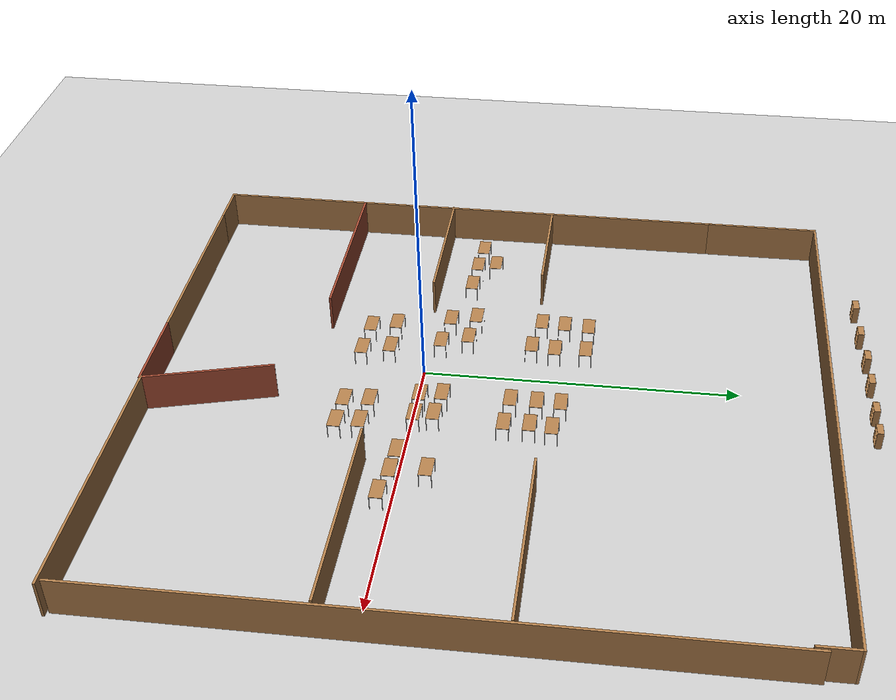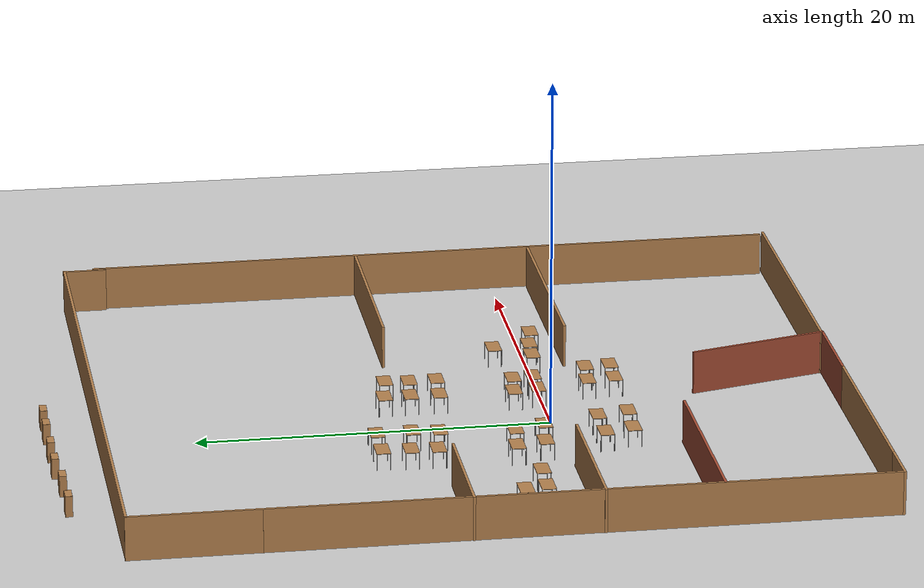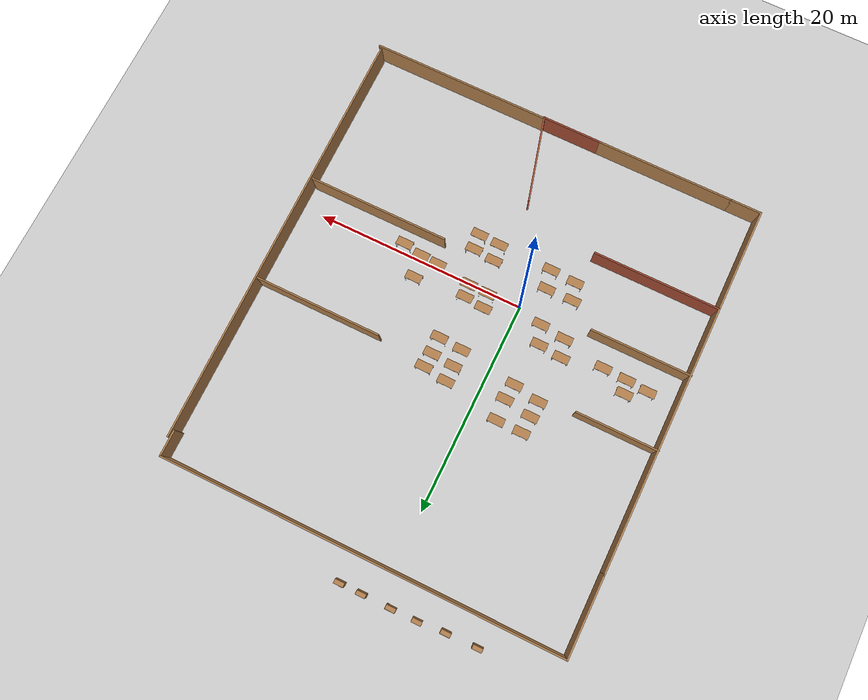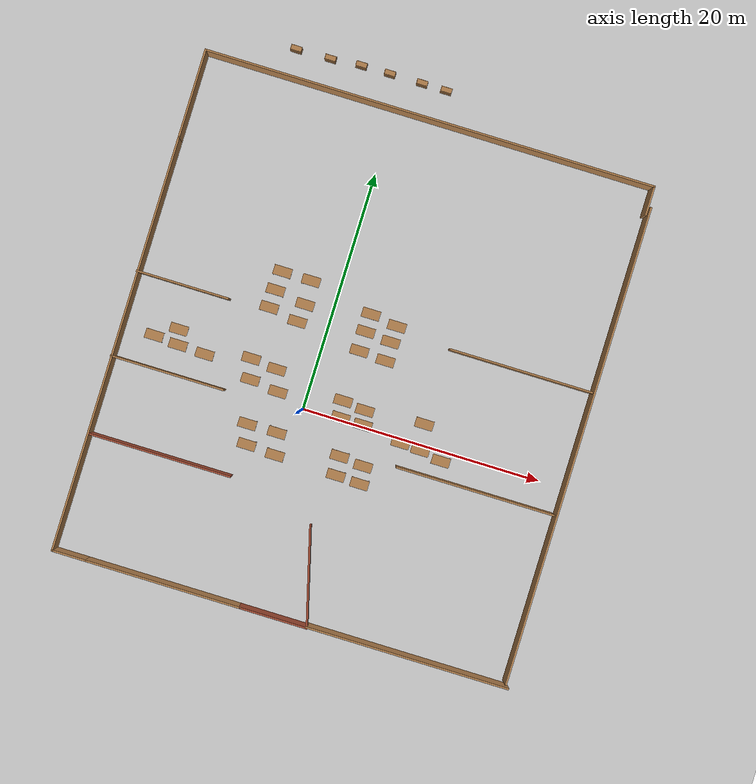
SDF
<sdf version="1.7">
 <world name="default">
  <light name="sun" type="directional">
   <pose>0 0 10 0 -0 0</pose>
   <diffuse>0.8 0.8 0.8 1</diffuse>
   <specular>0.2 0.2 0.2 1</specular>
   <attenuation>
    <range>1000</range>
    <constant>0.9</constant>
    <linear>0.01</linear>
    <quadratic>0.001</quadratic>
   </attenuation>
   <direction>-0.5 0.1 -0.9</direction>
   <spot><inner_angle>0</inner_angle><outer_angle>0</outer_angle><falloff>0</falloff></spot>
  </light>
  <model name="ground_plane">
   <static>1</static>
   <link name="link">
    <collision name="collision">
     <geometry><plane><normal>0 0 1</normal><size>100 100</size></plane></geometry>
     <surface>
      <contact><collide_bitmask>65535</collide_bitmask></contact>
      <friction><ode><mu>100</mu><mu2>50</mu2></ode></friction>
     </surface>
    </collision>
    <visual name="visual">
     <cast_shadows>0</cast_shadows>
     <geometry><plane><normal>0 0 1</normal><size>100 100</size></plane></geometry>
     <material>
      <script><uri>file://media/materials/scripts/gazebo.material</uri><name>Gazebo/Grey</name></script>
     </material>
    </visual>
   </link>
  </model>
  <gravity>0 0 -9.8</gravity>
  <magnetic_field>6e-06 2.3e-05 -4.2e-05</magnetic_field>
  <atmosphere type="adiabatic"/>
  <physics type="ode">
   <max_step_size>0.001</max_step_size>
   <real_time_factor>1</real_time_factor>
   <real_time_update_rate>1000</real_time_update_rate>
  </physics>
  <scene><ambient>0.4 0.4 0.4 1</ambient><background>0.7 0.7 0.7 1</background><shadows>1</shadows></scene>
  <audio><device>default</device></audio>
  <spherical_coordinates>
   <surface_model>EARTH_WGS84</surface_model>
   <latitude_deg>0</latitude_deg>
   <longitude_deg>0</longitude_deg>
   <elevation>0</elevation>
   <heading_deg>0</heading_deg>
  </spherical_coordinates>
  <model name="table">
   <static>1</static>
   <link name="link">
    <collision name="surface">
     <pose>0 0 1 0 -0 0</pose>
     <geometry><box><size>1.5 0.8 0.03</size></box></geometry>
     <surface><friction><ode><mu>0.6</mu><mu2>0.6</mu2></ode></friction></surface>
    </collision>
    <visual name="visual1">
     <pose>0 0 1 0 -0 0</pose>
     <geometry><box><size>1.5 0.8 0.03</size></box></geometry>
     <material>
      <script><uri>file://media/materials/scripts/gazebo.material</uri><name>Gazebo/Wood</name></script>
     </material>
    </visual>
    <collision name="front_left_leg">
     <pose>0.68 0.38 0.5 0 -0 0</pose>
     <geometry><cylinder><radius>0.02</radius><length>1</length></cylinder></geometry>
    </collision>
    <visual name="front_left_leg">
     <pose>0.68 0.38 0.5 0 -0 0</pose>
     <geometry><cylinder><radius>0.02</radius><length>1</length></cylinder></geometry>
     <material>
      <script><uri>file://media/materials/scripts/gazebo.material</uri><name>Gazebo/Grey</name></script>
     </material>
    </visual>
    <collision name="front_right_leg">
     <pose>0.68 -0.38 0.5 0 -0 0</pose>
     <geometry><cylinder><radius>0.02</radius><length>1</length></cylinder></geometry>
    </collision>
    <visual name="front_right_leg">
     <pose>0.68 -0.38 0.5 0 -0 0</pose>
     <geometry><cylinder><radius>0.02</radius><length>1</length></cylinder></geometry>
     <material>
      <script><uri>file://media/materials/scripts/gazebo.material</uri><name>Gazebo/Grey</name></script>
     </material>
    </visual>
    <collision name="back_right_leg">
     <pose>-0.68 -0.38 0.5 0 -0 0</pose>
     <geometry><cylinder><radius>0.02</radius><length>1</length></cylinder></geometry>
    </collision>
    <visual name="back_right_leg">
     <pose>-0.68 -0.38 0.5 0 -0 0</pose>
     <geometry><cylinder><radius>0.02</radius><length>1</length></cylinder></geometry>
     <material>
      <script><uri>file://media/materials/scripts/gazebo.material</uri><name>Gazebo/Grey</name></script>
     </material>
    </visual>
    <collision name="back_left_leg">
     <pose>-0.68 0.38 0.5 0 -0 0</pose>
     <geometry><cylinder><radius>0.02</radius><length>1</length></cylinder></geometry>
    </collision>
    <visual name="back_left_leg">
     <pose>-0.68 0.38 0.5 0 -0 0</pose>
     <geometry><cylinder><radius>0.02</radius><length>1</length></cylinder></geometry>
     <material>
      <script><uri>file://media/materials/scripts/gazebo.material</uri><name>Gazebo/Grey</name></script>
     </material>
    </visual>
   </link>
   <pose>3.92211 -2.73717 0 0 -0 0</pose>
  </model>
  <model name="table_clone">
   <static>1</static>
   <link name="link">
    <collision name="surface">
     <pose>0 0 1 0 -0 0</pose>
     <geometry><box><size>1.5 0.8 0.03</size></box></geometry>
     <surface><friction><ode><mu>0.6</mu><mu2>0.6</mu2></ode></friction></surface>
    </collision>
    <visual name="visual1">
     <pose>0 0 1 0 -0 0</pose>
     <geometry><box><size>1.5 0.8 0.03</size></box></geometry>
     <material>
      <script><uri>file://media/materials/scripts/gazebo.material</uri><name>Gazebo/Wood</name></script>
     </material>
    </visual>
    <collision name="front_left_leg">
     <pose>0.68 0.38 0.5 0 -0 0</pose>
     <geometry><cylinder><radius>0.02</radius><length>1</length></cylinder></geometry>
    </collision>
    <visual name="front_left_leg">
     <pose>0.68 0.38 0.5 0 -0 0</pose>
     <geometry><cylinder><radius>0.02</radius><length>1</length></cylinder></geometry>
     <material>
      <script><uri>file://media/materials/scripts/gazebo.material</uri><name>Gazebo/Grey</name></script>
     </material>
    </visual>
    <collision name="front_right_leg">
     <pose>0.68 -0.38 0.5 0 -0 0</pose>
     <geometry><cylinder><radius>0.02</radius><length>1</length></cylinder></geometry>
    </collision>
    <visual name="front_right_leg">
     <pose>0.68 -0.38 0.5 0 -0 0</pose>
     <geometry><cylinder><radius>0.02</radius><length>1</length></cylinder></geometry>
     <material>
      <script><uri>file://media/materials/scripts/gazebo.material</uri><name>Gazebo/Grey</name></script>
     </material>
    </visual>
    <collision name="back_right_leg">
     <pose>-0.68 -0.38 0.5 0 -0 0</pose>
     <geometry><cylinder><radius>0.02</radius><length>1</length></cylinder></geometry>
    </collision>
    <visual name="back_right_leg">
     <pose>-0.68 -0.38 0.5 0 -0 0</pose>
     <geometry><cylinder><radius>0.02</radius><length>1</length></cylinder></geometry>
     <material>
      <script><uri>file://media/materials/scripts/gazebo.material</uri><name>Gazebo/Grey</name></script>
     </material>
    </visual>
    <collision name="back_left_leg">
     <pose>-0.68 0.38 0.5 0 -0 0</pose>
     <geometry><cylinder><radius>0.02</radius><length>1</length></cylinder></geometry>
    </collision>
    <visual name="back_left_leg">
     <pose>-0.68 0.38 0.5 0 -0 0</pose>
     <geometry><cylinder><radius>0.02</radius><length>1</length></cylinder></geometry>
     <material>
      <script><uri>file://media/materials/scripts/gazebo.material</uri><name>Gazebo/Grey</name></script>
     </material>
    </visual>
   </link>
   <pose>5.97577 -2.95119 0 0 -0 0</pose>
  </model>
  <model name="table_clone_1">
   <static>1</static>
   <link name="link">
    <collision name="surface">
     <pose>0 0 1 0 -0 0</pose>
     <geometry><box><size>1.5 0.8 0.03</size></box></geometry>
     <surface><friction><ode><mu>0.6</mu><mu2>0.6</mu2></ode></friction></surface>
    </collision>
    <visual name="visual1">
     <pose>0 0 1 0 -0 0</pose>
     <geometry><box><size>1.5 0.8 0.03</size></box></geometry>
     <material>
      <script><uri>file://media/materials/scripts/gazebo.material</uri><name>Gazebo/Wood</name></script>
     </material>
    </visual>
    <collision name="front_left_leg">
     <pose>0.68 0.38 0.5 0 -0 0</pose>
     <geometry><cylinder><radius>0.02</radius><length>1</length></cylinder></geometry>
    </collision>
    <visual name="front_left_leg">
     <pose>0.68 0.38 0.5 0 -0 0</pose>
     <geometry><cylinder><radius>0.02</radius><length>1</length></cylinder></geometry>
     <material>
      <script><uri>file://media/materials/scripts/gazebo.material</uri><name>Gazebo/Grey</name></script>
     </material>
    </visual>
    <collision name="front_right_leg">
     <pose>0.68 -0.38 0.5 0 -0 0</pose>
     <geometry><cylinder><radius>0.02</radius><length>1</length></cylinder></geometry>
    </collision>
    <visual name="front_right_leg">
     <pose>0.68 -0.38 0.5 0 -0 0</pose>
     <geometry><cylinder><radius>0.02</radius><length>1</length></cylinder></geometry>
     <material>
      <script><uri>file://media/materials/scripts/gazebo.material</uri><name>Gazebo/Grey</name></script>
     </material>
    </visual>
    <collision name="back_right_leg">
     <pose>-0.68 -0.38 0.5 0 -0 0</pose>
     <geometry><cylinder><radius>0.02</radius><length>1</length></cylinder></geometry>
    </collision>
    <visual name="back_right_leg">
     <pose>-0.68 -0.38 0.5 0 -0 0</pose>
     <geometry><cylinder><radius>0.02</radius><length>1</length></cylinder></geometry>
     <material>
      <script><uri>file://media/materials/scripts/gazebo.material</uri><name>Gazebo/Grey</name></script>
     </material>
    </visual>
    <collision name="back_left_leg">
     <pose>-0.68 0.38 0.5 0 -0 0</pose>
     <geometry><cylinder><radius>0.02</radius><length>1</length></cylinder></geometry>
    </collision>
    <visual name="back_left_leg">
     <pose>-0.68 0.38 0.5 0 -0 0</pose>
     <geometry><cylinder><radius>0.02</radius><length>1</length></cylinder></geometry>
     <material>
      <script><uri>file://media/materials/scripts/gazebo.material</uri><name>Gazebo/Grey</name></script>
     </material>
    </visual>
   </link>
   <pose>6.11176 -4.39792 0 0 -0 0</pose>
  </model>
  <model name="table_clone_2">
   <static>1</static>
   <link name="link">
    <collision name="surface">
     <pose>0 0 1 0 -0 0</pose>
     <geometry><box><size>1.5 0.8 0.03</size></box></geometry>
     <surface><friction><ode><mu>0.6</mu><mu2>0.6</mu2></ode></friction></surface>
    </collision>
    <visual name="visual1">
     <pose>0 0 1 0 -0 0</pose>
     <geometry><box><size>1.5 0.8 0.03</size></box></geometry>
     <material>
      <script><uri>file://media/materials/scripts/gazebo.material</uri><name>Gazebo/Wood</name></script>
     </material>
    </visual>
    <collision name="front_left_leg">
     <pose>0.68 0.38 0.5 0 -0 0</pose>
     <geometry><cylinder><radius>0.02</radius><length>1</length></cylinder></geometry>
    </collision>
    <visual name="front_left_leg">
     <pose>0.68 0.38 0.5 0 -0 0</pose>
     <geometry><cylinder><radius>0.02</radius><length>1</length></cylinder></geometry>
     <material>
      <script><uri>file://media/materials/scripts/gazebo.material</uri><name>Gazebo/Grey</name></script>
     </material>
    </visual>
    <collision name="front_right_leg">
     <pose>0.68 -0.38 0.5 0 -0 0</pose>
     <geometry><cylinder><radius>0.02</radius><length>1</length></cylinder></geometry>
    </collision>
    <visual name="front_right_leg">
     <pose>0.68 -0.38 0.5 0 -0 0</pose>
     <geometry><cylinder><radius>0.02</radius><length>1</length></cylinder></geometry>
     <material>
      <script><uri>file://media/materials/scripts/gazebo.material</uri><name>Gazebo/Grey</name></script>
     </material>
    </visual>
    <collision name="back_right_leg">
     <pose>-0.68 -0.38 0.5 0 -0 0</pose>
     <geometry><cylinder><radius>0.02</radius><length>1</length></cylinder></geometry>
    </collision>
    <visual name="back_right_leg">
     <pose>-0.68 -0.38 0.5 0 -0 0</pose>
     <geometry><cylinder><radius>0.02</radius><length>1</length></cylinder></geometry>
     <material>
      <script><uri>file://media/materials/scripts/gazebo.material</uri><name>Gazebo/Grey</name></script>
     </material>
    </visual>
    <collision name="back_left_leg">
     <pose>-0.68 0.38 0.5 0 -0 0</pose>
     <geometry><cylinder><radius>0.02</radius><length>1</length></cylinder></geometry>
    </collision>
    <visual name="back_left_leg">
     <pose>-0.68 0.38 0.5 0 -0 0</pose>
     <geometry><cylinder><radius>0.02</radius><length>1</length></cylinder></geometry>
     <material>
      <script><uri>file://media/materials/scripts/gazebo.material</uri><name>Gazebo/Grey</name></script>
     </material>
    </visual>
   </link>
   <pose>-1.48 -2.39226 0 0 -0 0</pose>
  </model>
  <model name="table_clone_3">
   <static>1</static>
   <link name="link">
    <collision name="surface">
     <pose>0 0 1 0 -0 0</pose>
     <geometry><box><size>1.5 0.8 0.03</size></box></geometry>
     <surface><friction><ode><mu>0.6</mu><mu2>0.6</mu2></ode></friction></surface>
    </collision>
    <visual name="visual1">
     <pose>0 0 1 0 -0 0</pose>
     <geometry><box><size>1.5 0.8 0.03</size></box></geometry>
     <material>
      <script><uri>file://media/materials/scripts/gazebo.material</uri><name>Gazebo/Wood</name></script>
     </material>
    </visual>
    <collision name="front_left_leg">
     <pose>0.68 0.38 0.5 0 -0 0</pose>
     <geometry><cylinder><radius>0.02</radius><length>1</length></cylinder></geometry>
    </collision>
    <visual name="front_left_leg">
     <pose>0.68 0.38 0.5 0 -0 0</pose>
     <geometry><cylinder><radius>0.02</radius><length>1</length></cylinder></geometry>
     <material>
      <script><uri>file://media/materials/scripts/gazebo.material</uri><name>Gazebo/Grey</name></script>
     </material>
    </visual>
    <collision name="front_right_leg">
     <pose>0.68 -0.38 0.5 0 -0 0</pose>
     <geometry><cylinder><radius>0.02</radius><length>1</length></cylinder></geometry>
    </collision>
    <visual name="front_right_leg">
     <pose>0.68 -0.38 0.5 0 -0 0</pose>
     <geometry><cylinder><radius>0.02</radius><length>1</length></cylinder></geometry>
     <material>
      <script><uri>file://media/materials/scripts/gazebo.material</uri><name>Gazebo/Grey</name></script>
     </material>
    </visual>
    <collision name="back_right_leg">
     <pose>-0.68 -0.38 0.5 0 -0 0</pose>
     <geometry><cylinder><radius>0.02</radius><length>1</length></cylinder></geometry>
    </collision>
    <visual name="back_right_leg">
     <pose>-0.68 -0.38 0.5 0 -0 0</pose>
     <geometry><cylinder><radius>0.02</radius><length>1</length></cylinder></geometry>
     <material>
      <script><uri>file://media/materials/scripts/gazebo.material</uri><name>Gazebo/Grey</name></script>
     </material>
    </visual>
    <collision name="back_left_leg">
     <pose>-0.68 0.38 0.5 0 -0 0</pose>
     <geometry><cylinder><radius>0.02</radius><length>1</length></cylinder></geometry>
    </collision>
    <visual name="back_left_leg">
     <pose>-0.68 0.38 0.5 0 -0 0</pose>
     <geometry><cylinder><radius>0.02</radius><length>1</length></cylinder></geometry>
     <material>
      <script><uri>file://media/materials/scripts/gazebo.material</uri><name>Gazebo/Grey</name></script>
     </material>
    </visual>
   </link>
   <pose>-3.97626 -2.40472 0 0 -0 0</pose>
  </model>
  <model name="table_clone_4">
   <static>1</static>
   <link name="link">
    <collision name="surface">
     <pose>0 0 1 0 -0 0</pose>
     <geometry><box><size>1.5 0.8 0.03</size></box></geometry>
     <surface><friction><ode><mu>0.6</mu><mu2>0.6</mu2></ode></friction></surface>
    </collision>
    <visual name="visual1">
     <pose>0 0 1 0 -0 0</pose>
     <geometry><box><size>1.5 0.8 0.03</size></box></geometry>
     <material>
      <script><uri>file://media/materials/scripts/gazebo.material</uri><name>Gazebo/Wood</name></script>
     </material>
    </visual>
    <collision name="front_left_leg">
     <pose>0.68 0.38 0.5 0 -0 0</pose>
     <geometry><cylinder><radius>0.02</radius><length>1</length></cylinder></geometry>
    </collision>
    <visual name="front_left_leg">
     <pose>0.68 0.38 0.5 0 -0 0</pose>
     <geometry><cylinder><radius>0.02</radius><length>1</length></cylinder></geometry>
     <material>
      <script><uri>file://media/materials/scripts/gazebo.material</uri><name>Gazebo/Grey</name></script>
     </material>
    </visual>
    <collision name="front_right_leg">
     <pose>0.68 -0.38 0.5 0 -0 0</pose>
     <geometry><cylinder><radius>0.02</radius><length>1</length></cylinder></geometry>
    </collision>
    <visual name="front_right_leg">
     <pose>0.68 -0.38 0.5 0 -0 0</pose>
     <geometry><cylinder><radius>0.02</radius><length>1</length></cylinder></geometry>
     <material>
      <script><uri>file://media/materials/scripts/gazebo.material</uri><name>Gazebo/Grey</name></script>
     </material>
    </visual>
    <collision name="back_right_leg">
     <pose>-0.68 -0.38 0.5 0 -0 0</pose>
     <geometry><cylinder><radius>0.02</radius><length>1</length></cylinder></geometry>
    </collision>
    <visual name="back_right_leg">
     <pose>-0.68 -0.38 0.5 0 -0 0</pose>
     <geometry><cylinder><radius>0.02</radius><length>1</length></cylinder></geometry>
     <material>
      <script><uri>file://media/materials/scripts/gazebo.material</uri><name>Gazebo/Grey</name></script>
     </material>
    </visual>
    <collision name="back_left_leg">
     <pose>-0.68 0.38 0.5 0 -0 0</pose>
     <geometry><cylinder><radius>0.02</radius><length>1</length></cylinder></geometry>
    </collision>
    <visual name="back_left_leg">
     <pose>-0.68 0.38 0.5 0 -0 0</pose>
     <geometry><cylinder><radius>0.02</radius><length>1</length></cylinder></geometry>
     <material>
      <script><uri>file://media/materials/scripts/gazebo.material</uri><name>Gazebo/Grey</name></script>
     </material>
    </visual>
   </link>
   <pose>-3.53618 -4.01867 0 0 -0 0</pose>
  </model>
  <model name="table_clone_5">
   <static>1</static>
   <link name="link">
    <collision name="surface">
     <pose>0 0 1 0 -0 0</pose>
     <geometry><box><size>1.5 0.8 0.03</size></box></geometry>
     <surface><friction><ode><mu>0.6</mu><mu2>0.6</mu2></ode></friction></surface>
    </collision>
    <visual name="visual1">
     <pose>0 0 1 0 -0 0</pose>
     <geometry><box><size>1.5 0.8 0.03</size></box></geometry>
     <material>
      <script><uri>file://media/materials/scripts/gazebo.material</uri><name>Gazebo/Wood</name></script>
     </material>
    </visual>
    <collision name="front_left_leg">
     <pose>0.68 0.38 0.5 0 -0 0</pose>
     <geometry><cylinder><radius>0.02</radius><length>1</length></cylinder></geometry>
    </collision>
    <visual name="front_left_leg">
     <pose>0.68 0.38 0.5 0 -0 0</pose>
     <geometry><cylinder><radius>0.02</radius><length>1</length></cylinder></geometry>
     <material>
      <script><uri>file://media/materials/scripts/gazebo.material</uri><name>Gazebo/Grey</name></script>
     </material>
    </visual>
    <collision name="front_right_leg">
     <pose>0.68 -0.38 0.5 0 -0 0</pose>
     <geometry><cylinder><radius>0.02</radius><length>1</length></cylinder></geometry>
    </collision>
    <visual name="front_right_leg">
     <pose>0.68 -0.38 0.5 0 -0 0</pose>
     <geometry><cylinder><radius>0.02</radius><length>1</length></cylinder></geometry>
     <material>
      <script><uri>file://media/materials/scripts/gazebo.material</uri><name>Gazebo/Grey</name></script>
     </material>
    </visual>
    <collision name="back_right_leg">
     <pose>-0.68 -0.38 0.5 0 -0 0</pose>
     <geometry><cylinder><radius>0.02</radius><length>1</length></cylinder></geometry>
    </collision>
    <visual name="back_right_leg">
     <pose>-0.68 -0.38 0.5 0 -0 0</pose>
     <geometry><cylinder><radius>0.02</radius><length>1</length></cylinder></geometry>
     <material>
      <script><uri>file://media/materials/scripts/gazebo.material</uri><name>Gazebo/Grey</name></script>
     </material>
    </visual>
    <collision name="back_left_leg">
     <pose>-0.68 0.38 0.5 0 -0 0</pose>
     <geometry><cylinder><radius>0.02</radius><length>1</length></cylinder></geometry>
    </collision>
    <visual name="back_left_leg">
     <pose>-0.68 0.38 0.5 0 -0 0</pose>
     <geometry><cylinder><radius>0.02</radius><length>1</length></cylinder></geometry>
     <material>
      <script><uri>file://media/materials/scripts/gazebo.material</uri><name>Gazebo/Grey</name></script>
     </material>
    </visual>
   </link>
   <pose>-1.10425 -4.17106 0 0 -0 0</pose>
  </model>
  <model name="table_clone_6">
   <static>1</static>
   <link name="link">
    <collision name="surface">
     <pose>0 0 1 0 -0 0</pose>
     <geometry><box><size>1.5 0.8 0.03</size></box></geometry>
     <surface><friction><ode><mu>0.6</mu><mu2>0.6</mu2></ode></friction></surface>
    </collision>
    <visual name="visual1">
     <pose>0 0 1 0 -0 0</pose>
     <geometry><box><size>1.5 0.8 0.03</size></box></geometry>
     <material>
      <script><uri>file://media/materials/scripts/gazebo.material</uri><name>Gazebo/Wood</name></script>
     </material>
    </visual>
    <collision name="front_left_leg">
     <pose>0.68 0.38 0.5 0 -0 0</pose>
     <geometry><cylinder><radius>0.02</radius><length>1</length></cylinder></geometry>
    </collision>
    <visual name="front_left_leg">
     <pose>0.68 0.38 0.5 0 -0 0</pose>
     <geometry><cylinder><radius>0.02</radius><length>1</length></cylinder></geometry>
     <material>
      <script><uri>file://media/materials/scripts/gazebo.material</uri><name>Gazebo/Grey</name></script>
     </material>
    </visual>
    <collision name="front_right_leg">
     <pose>0.68 -0.38 0.5 0 -0 0</pose>
     <geometry><cylinder><radius>0.02</radius><length>1</length></cylinder></geometry>
    </collision>
    <visual name="front_right_leg">
     <pose>0.68 -0.38 0.5 0 -0 0</pose>
     <geometry><cylinder><radius>0.02</radius><length>1</length></cylinder></geometry>
     <material>
      <script><uri>file://media/materials/scripts/gazebo.material</uri><name>Gazebo/Grey</name></script>
     </material>
    </visual>
    <collision name="back_right_leg">
     <pose>-0.68 -0.38 0.5 0 -0 0</pose>
     <geometry><cylinder><radius>0.02</radius><length>1</length></cylinder></geometry>
    </collision>
    <visual name="back_right_leg">
     <pose>-0.68 -0.38 0.5 0 -0 0</pose>
     <geometry><cylinder><radius>0.02</radius><length>1</length></cylinder></geometry>
     <material>
      <script><uri>file://media/materials/scripts/gazebo.material</uri><name>Gazebo/Grey</name></script>
     </material>
    </visual>
    <collision name="back_left_leg">
     <pose>-0.68 0.38 0.5 0 -0 0</pose>
     <geometry><cylinder><radius>0.02</radius><length>1</length></cylinder></geometry>
    </collision>
    <visual name="back_left_leg">
     <pose>-0.68 0.38 0.5 0 -0 0</pose>
     <geometry><cylinder><radius>0.02</radius><length>1</length></cylinder></geometry>
     <material>
      <script><uri>file://media/materials/scripts/gazebo.material</uri><name>Gazebo/Grey</name></script>
     </material>
    </visual>
   </link>
   <pose>-4.7921 1.09952 0 0 -0 0</pose>
  </model>
  <model name="table_clone_7">
   <static>1</static>
   <link name="link">
    <collision name="surface">
     <pose>0 0 1 0 -0 0</pose>
     <geometry><box><size>1.5 0.8 0.03</size></box></geometry>
     <surface><friction><ode><mu>0.6</mu><mu2>0.6</mu2></ode></friction></surface>
    </collision>
    <visual name="visual1">
     <pose>0 0 1 0 -0 0</pose>
     <geometry><box><size>1.5 0.8 0.03</size></box></geometry>
     <material>
      <script><uri>file://media/materials/scripts/gazebo.material</uri><name>Gazebo/Wood</name></script>
     </material>
    </visual>
    <collision name="front_left_leg">
     <pose>0.68 0.38 0.5 0 -0 0</pose>
     <geometry><cylinder><radius>0.02</radius><length>1</length></cylinder></geometry>
    </collision>
    <visual name="front_left_leg">
     <pose>0.68 0.38 0.5 0 -0 0</pose>
     <geometry><cylinder><radius>0.02</radius><length>1</length></cylinder></geometry>
     <material>
      <script><uri>file://media/materials/scripts/gazebo.material</uri><name>Gazebo/Grey</name></script>
     </material>
    </visual>
    <collision name="front_right_leg">
     <pose>0.68 -0.38 0.5 0 -0 0</pose>
     <geometry><cylinder><radius>0.02</radius><length>1</length></cylinder></geometry>
    </collision>
    <visual name="front_right_leg">
     <pose>0.68 -0.38 0.5 0 -0 0</pose>
     <geometry><cylinder><radius>0.02</radius><length>1</length></cylinder></geometry>
     <material>
      <script><uri>file://media/materials/scripts/gazebo.material</uri><name>Gazebo/Grey</name></script>
     </material>
    </visual>
    <collision name="back_right_leg">
     <pose>-0.68 -0.38 0.5 0 -0 0</pose>
     <geometry><cylinder><radius>0.02</radius><length>1</length></cylinder></geometry>
    </collision>
    <visual name="back_right_leg">
     <pose>-0.68 -0.38 0.5 0 -0 0</pose>
     <geometry><cylinder><radius>0.02</radius><length>1</length></cylinder></geometry>
     <material>
      <script><uri>file://media/materials/scripts/gazebo.material</uri><name>Gazebo/Grey</name></script>
     </material>
    </visual>
    <collision name="back_left_leg">
     <pose>-0.68 0.38 0.5 0 -0 0</pose>
     <geometry><cylinder><radius>0.02</radius><length>1</length></cylinder></geometry>
    </collision>
    <visual name="back_left_leg">
     <pose>-0.68 0.38 0.5 0 -0 0</pose>
     <geometry><cylinder><radius>0.02</radius><length>1</length></cylinder></geometry>
     <material>
      <script><uri>file://media/materials/scripts/gazebo.material</uri><name>Gazebo/Grey</name></script>
     </material>
    </visual>
   </link>
   <pose>-2.37165 0.786357 0 0 -0 0</pose>
  </model>
  <model name="table_clone_8">
   <static>1</static>
   <link name="link">
    <collision name="surface">
     <pose>0 0 1 0 -0 0</pose>
     <geometry><box><size>1.5 0.8 0.03</size></box></geometry>
     <surface><friction><ode><mu>0.6</mu><mu2>0.6</mu2></ode></friction></surface>
    </collision>
    <visual name="visual1">
     <pose>0 0 1 0 -0 0</pose>
     <geometry><box><size>1.5 0.8 0.03</size></box></geometry>
     <material>
      <script><uri>file://media/materials/scripts/gazebo.material</uri><name>Gazebo/Wood</name></script>
     </material>
    </visual>
    <collision name="front_left_leg">
     <pose>0.68 0.38 0.5 0 -0 0</pose>
     <geometry><cylinder><radius>0.02</radius><length>1</length></cylinder></geometry>
    </collision>
    <visual name="front_left_leg">
     <pose>0.68 0.38 0.5 0 -0 0</pose>
     <geometry><cylinder><radius>0.02</radius><length>1</length></cylinder></geometry>
     <material>
      <script><uri>file://media/materials/scripts/gazebo.material</uri><name>Gazebo/Grey</name></script>
     </material>
    </visual>
    <collision name="front_right_leg">
     <pose>0.68 -0.38 0.5 0 -0 0</pose>
     <geometry><cylinder><radius>0.02</radius><length>1</length></cylinder></geometry>
    </collision>
    <visual name="front_right_leg">
     <pose>0.68 -0.38 0.5 0 -0 0</pose>
     <geometry><cylinder><radius>0.02</radius><length>1</length></cylinder></geometry>
     <material>
      <script><uri>file://media/materials/scripts/gazebo.material</uri><name>Gazebo/Grey</name></script>
     </material>
    </visual>
    <collision name="back_right_leg">
     <pose>-0.68 -0.38 0.5 0 -0 0</pose>
     <geometry><cylinder><radius>0.02</radius><length>1</length></cylinder></geometry>
    </collision>
    <visual name="back_right_leg">
     <pose>-0.68 -0.38 0.5 0 -0 0</pose>
     <geometry><cylinder><radius>0.02</radius><length>1</length></cylinder></geometry>
     <material>
      <script><uri>file://media/materials/scripts/gazebo.material</uri><name>Gazebo/Grey</name></script>
     </material>
    </visual>
    <collision name="back_left_leg">
     <pose>-0.68 0.38 0.5 0 -0 0</pose>
     <geometry><cylinder><radius>0.02</radius><length>1</length></cylinder></geometry>
    </collision>
    <visual name="back_left_leg">
     <pose>-0.68 0.38 0.5 0 -0 0</pose>
     <geometry><cylinder><radius>0.02</radius><length>1</length></cylinder></geometry>
     <material>
      <script><uri>file://media/materials/scripts/gazebo.material</uri><name>Gazebo/Grey</name></script>
     </material>
    </visual>
   </link>
   <pose>-5.22061 2.75094 0 0 -0 0</pose>
  </model>
  <model name="table_clone_9">
   <static>1</static>
   <link name="link">
    <collision name="surface">
     <pose>0 0 1 0 -0 0</pose>
     <geometry><box><size>1.5 0.8 0.03</size></box></geometry>
     <surface><friction><ode><mu>0.6</mu><mu2>0.6</mu2></ode></friction></surface>
    </collision>
    <visual name="visual1">
     <pose>0 0 1 0 -0 0</pose>
     <geometry><box><size>1.5 0.8 0.03</size></box></geometry>
     <material>
      <script><uri>file://media/materials/scripts/gazebo.material</uri><name>Gazebo/Wood</name></script>
     </material>
    </visual>
    <collision name="front_left_leg">
     <pose>0.68 0.38 0.5 0 -0 0</pose>
     <geometry><cylinder><radius>0.02</radius><length>1</length></cylinder></geometry>
    </collision>
    <visual name="front_left_leg">
     <pose>0.68 0.38 0.5 0 -0 0</pose>
     <geometry><cylinder><radius>0.02</radius><length>1</length></cylinder></geometry>
     <material>
      <script><uri>file://media/materials/scripts/gazebo.material</uri><name>Gazebo/Grey</name></script>
     </material>
    </visual>
    <collision name="front_right_leg">
     <pose>0.68 -0.38 0.5 0 -0 0</pose>
     <geometry><cylinder><radius>0.02</radius><length>1</length></cylinder></geometry>
    </collision>
    <visual name="front_right_leg">
     <pose>0.68 -0.38 0.5 0 -0 0</pose>
     <geometry><cylinder><radius>0.02</radius><length>1</length></cylinder></geometry>
     <material>
      <script><uri>file://media/materials/scripts/gazebo.material</uri><name>Gazebo/Grey</name></script>
     </material>
    </visual>
    <collision name="back_right_leg">
     <pose>-0.68 -0.38 0.5 0 -0 0</pose>
     <geometry><cylinder><radius>0.02</radius><length>1</length></cylinder></geometry>
    </collision>
    <visual name="back_right_leg">
     <pose>-0.68 -0.38 0.5 0 -0 0</pose>
     <geometry><cylinder><radius>0.02</radius><length>1</length></cylinder></geometry>
     <material>
      <script><uri>file://media/materials/scripts/gazebo.material</uri><name>Gazebo/Grey</name></script>
     </material>
    </visual>
    <collision name="back_left_leg">
     <pose>-0.68 0.38 0.5 0 -0 0</pose>
     <geometry><cylinder><radius>0.02</radius><length>1</length></cylinder></geometry>
    </collision>
    <visual name="back_left_leg">
     <pose>-0.68 0.38 0.5 0 -0 0</pose>
     <geometry><cylinder><radius>0.02</radius><length>1</length></cylinder></geometry>
     <material>
      <script><uri>file://media/materials/scripts/gazebo.material</uri><name>Gazebo/Grey</name></script>
     </material>
    </visual>
   </link>
   <pose>-2.99759 2.50603 0 0 -0 0</pose>
  </model>
  <model name="table_clone_10">
   <static>1</static>
   <link name="link">
    <collision name="surface">
     <pose>0 0 1 0 -0 0</pose>
     <geometry><box><size>1.5 0.8 0.03</size></box></geometry>
     <surface><friction><ode><mu>0.6</mu><mu2>0.6</mu2></ode></friction></surface>
    </collision>
    <visual name="visual1">
     <pose>0 0 1 0 -0 0</pose>
     <geometry><box><size>1.5 0.8 0.03</size></box></geometry>
     <material>
      <script><uri>file://media/materials/scripts/gazebo.material</uri><name>Gazebo/Wood</name></script>
     </material>
    </visual>
    <collision name="front_left_leg">
     <pose>0.68 0.38 0.5 0 -0 0</pose>
     <geometry><cylinder><radius>0.02</radius><length>1</length></cylinder></geometry>
    </collision>
    <visual name="front_left_leg">
     <pose>0.68 0.38 0.5 0 -0 0</pose>
     <geometry><cylinder><radius>0.02</radius><length>1</length></cylinder></geometry>
     <material>
      <script><uri>file://media/materials/scripts/gazebo.material</uri><name>Gazebo/Grey</name></script>
     </material>
    </visual>
    <collision name="front_right_leg">
     <pose>0.68 -0.38 0.5 0 -0 0</pose>
     <geometry><cylinder><radius>0.02</radius><length>1</length></cylinder></geometry>
    </collision>
    <visual name="front_right_leg">
     <pose>0.68 -0.38 0.5 0 -0 0</pose>
     <geometry><cylinder><radius>0.02</radius><length>1</length></cylinder></geometry>
     <material>
      <script><uri>file://media/materials/scripts/gazebo.material</uri><name>Gazebo/Grey</name></script>
     </material>
    </visual>
    <collision name="back_right_leg">
     <pose>-0.68 -0.38 0.5 0 -0 0</pose>
     <geometry><cylinder><radius>0.02</radius><length>1</length></cylinder></geometry>
    </collision>
    <visual name="back_right_leg">
     <pose>-0.68 -0.38 0.5 0 -0 0</pose>
     <geometry><cylinder><radius>0.02</radius><length>1</length></cylinder></geometry>
     <material>
      <script><uri>file://media/materials/scripts/gazebo.material</uri><name>Gazebo/Grey</name></script>
     </material>
    </visual>
    <collision name="back_left_leg">
     <pose>-0.68 0.38 0.5 0 -0 0</pose>
     <geometry><cylinder><radius>0.02</radius><length>1</length></cylinder></geometry>
    </collision>
    <visual name="back_left_leg">
     <pose>-0.68 0.38 0.5 0 -0 0</pose>
     <geometry><cylinder><radius>0.02</radius><length>1</length></cylinder></geometry>
     <material>
      <script><uri>file://media/materials/scripts/gazebo.material</uri><name>Gazebo/Grey</name></script>
     </material>
    </visual>
   </link>
   <pose>3.09567 0.266723 0 0 -0 0</pose>
  </model>
  <model name="table_clone_11">
   <static>1</static>
   <link name="link">
    <collision name="surface">
     <pose>0 0 1 0 -0 0</pose>
     <geometry><box><size>1.5 0.8 0.03</size></box></geometry>
     <surface><friction><ode><mu>0.6</mu><mu2>0.6</mu2></ode></friction></surface>
    </collision>
    <visual name="visual1">
     <pose>0 0 1 0 -0 0</pose>
     <geometry><box><size>1.5 0.8 0.03</size></box></geometry>
     <material>
      <script><uri>file://media/materials/scripts/gazebo.material</uri><name>Gazebo/Wood</name></script>
     </material>
    </visual>
    <collision name="front_left_leg">
     <pose>0.68 0.38 0.5 0 -0 0</pose>
     <geometry><cylinder><radius>0.02</radius><length>1</length></cylinder></geometry>
    </collision>
    <visual name="front_left_leg">
     <pose>0.68 0.38 0.5 0 -0 0</pose>
     <geometry><cylinder><radius>0.02</radius><length>1</length></cylinder></geometry>
     <material>
      <script><uri>file://media/materials/scripts/gazebo.material</uri><name>Gazebo/Grey</name></script>
     </material>
    </visual>
    <collision name="front_right_leg">
     <pose>0.68 -0.38 0.5 0 -0 0</pose>
     <geometry><cylinder><radius>0.02</radius><length>1</length></cylinder></geometry>
    </collision>
    <visual name="front_right_leg">
     <pose>0.68 -0.38 0.5 0 -0 0</pose>
     <geometry><cylinder><radius>0.02</radius><length>1</length></cylinder></geometry>
     <material>
      <script><uri>file://media/materials/scripts/gazebo.material</uri><name>Gazebo/Grey</name></script>
     </material>
    </visual>
    <collision name="back_right_leg">
     <pose>-0.68 -0.38 0.5 0 -0 0</pose>
     <geometry><cylinder><radius>0.02</radius><length>1</length></cylinder></geometry>
    </collision>
    <visual name="back_right_leg">
     <pose>-0.68 -0.38 0.5 0 -0 0</pose>
     <geometry><cylinder><radius>0.02</radius><length>1</length></cylinder></geometry>
     <material>
      <script><uri>file://media/materials/scripts/gazebo.material</uri><name>Gazebo/Grey</name></script>
     </material>
    </visual>
    <collision name="back_left_leg">
     <pose>-0.68 0.38 0.5 0 -0 0</pose>
     <geometry><cylinder><radius>0.02</radius><length>1</length></cylinder></geometry>
    </collision>
    <visual name="back_left_leg">
     <pose>-0.68 0.38 0.5 0 -0 0</pose>
     <geometry><cylinder><radius>0.02</radius><length>1</length></cylinder></geometry>
     <material>
      <script><uri>file://media/materials/scripts/gazebo.material</uri><name>Gazebo/Grey</name></script>
     </material>
    </visual>
   </link>
   <pose>4.98145 0.226839 0 0 -0 0</pose>
  </model>
  <model name="table_clone_12">
   <static>1</static>
   <link name="link">
    <collision name="surface">
     <pose>0 0 1 0 -0 0</pose>
     <geometry><box><size>1.5 0.8 0.03</size></box></geometry>
     <surface><friction><ode><mu>0.6</mu><mu2>0.6</mu2></ode></friction></surface>
    </collision>
    <visual name="visual1">
     <pose>0 0 1 0 -0 0</pose>
     <geometry><box><size>1.5 0.8 0.03</size></box></geometry>
     <material>
      <script><uri>file://media/materials/scripts/gazebo.material</uri><name>Gazebo/Wood</name></script>
     </material>
    </visual>
    <collision name="front_left_leg">
     <pose>0.68 0.38 0.5 0 -0 0</pose>
     <geometry><cylinder><radius>0.02</radius><length>1</length></cylinder></geometry>
    </collision>
    <visual name="front_left_leg">
     <pose>0.68 0.38 0.5 0 -0 0</pose>
     <geometry><cylinder><radius>0.02</radius><length>1</length></cylinder></geometry>
     <material>
      <script><uri>file://media/materials/scripts/gazebo.material</uri><name>Gazebo/Grey</name></script>
     </material>
    </visual>
    <collision name="front_right_leg">
     <pose>0.68 -0.38 0.5 0 -0 0</pose>
     <geometry><cylinder><radius>0.02</radius><length>1</length></cylinder></geometry>
    </collision>
    <visual name="front_right_leg">
     <pose>0.68 -0.38 0.5 0 -0 0</pose>
     <geometry><cylinder><radius>0.02</radius><length>1</length></cylinder></geometry>
     <material>
      <script><uri>file://media/materials/scripts/gazebo.material</uri><name>Gazebo/Grey</name></script>
     </material>
    </visual>
    <collision name="back_right_leg">
     <pose>-0.68 -0.38 0.5 0 -0 0</pose>
     <geometry><cylinder><radius>0.02</radius><length>1</length></cylinder></geometry>
    </collision>
    <visual name="back_right_leg">
     <pose>-0.68 -0.38 0.5 0 -0 0</pose>
     <geometry><cylinder><radius>0.02</radius><length>1</length></cylinder></geometry>
     <material>
      <script><uri>file://media/materials/scripts/gazebo.material</uri><name>Gazebo/Grey</name></script>
     </material>
    </visual>
    <collision name="back_left_leg">
     <pose>-0.68 0.38 0.5 0 -0 0</pose>
     <geometry><cylinder><radius>0.02</radius><length>1</length></cylinder></geometry>
    </collision>
    <visual name="back_left_leg">
     <pose>-0.68 0.38 0.5 0 -0 0</pose>
     <geometry><cylinder><radius>0.02</radius><length>1</length></cylinder></geometry>
     <material>
      <script><uri>file://media/materials/scripts/gazebo.material</uri><name>Gazebo/Grey</name></script>
     </material>
    </visual>
   </link>
   <pose>2.89121 1.63907 0 0 -0 0</pose>
  </model>
  <model name="table_clone_13">
   <static>1</static>
   <link name="link">
    <collision name="surface">
     <pose>0 0 1 0 -0 0</pose>
     <geometry><box><size>1.5 0.8 0.03</size></box></geometry>
     <surface><friction><ode><mu>0.6</mu><mu2>0.6</mu2></ode></friction></surface>
    </collision>
    <visual name="visual1">
     <pose>0 0 1 0 -0 0</pose>
     <geometry><box><size>1.5 0.8 0.03</size></box></geometry>
     <material>
      <script><uri>file://media/materials/scripts/gazebo.material</uri><name>Gazebo/Wood</name></script>
     </material>
    </visual>
    <collision name="front_left_leg">
     <pose>0.68 0.38 0.5 0 -0 0</pose>
     <geometry><cylinder><radius>0.02</radius><length>1</length></cylinder></geometry>
    </collision>
    <visual name="front_left_leg">
     <pose>0.68 0.38 0.5 0 -0 0</pose>
     <geometry><cylinder><radius>0.02</radius><length>1</length></cylinder></geometry>
     <material>
      <script><uri>file://media/materials/scripts/gazebo.material</uri><name>Gazebo/Grey</name></script>
     </material>
    </visual>
    <collision name="front_right_leg">
     <pose>0.68 -0.38 0.5 0 -0 0</pose>
     <geometry><cylinder><radius>0.02</radius><length>1</length></cylinder></geometry>
    </collision>
    <visual name="front_right_leg">
     <pose>0.68 -0.38 0.5 0 -0 0</pose>
     <geometry><cylinder><radius>0.02</radius><length>1</length></cylinder></geometry>
     <material>
      <script><uri>file://media/materials/scripts/gazebo.material</uri><name>Gazebo/Grey</name></script>
     </material>
    </visual>
    <collision name="back_right_leg">
     <pose>-0.68 -0.38 0.5 0 -0 0</pose>
     <geometry><cylinder><radius>0.02</radius><length>1</length></cylinder></geometry>
    </collision>
    <visual name="back_right_leg">
     <pose>-0.68 -0.38 0.5 0 -0 0</pose>
     <geometry><cylinder><radius>0.02</radius><length>1</length></cylinder></geometry>
     <material>
      <script><uri>file://media/materials/scripts/gazebo.material</uri><name>Gazebo/Grey</name></script>
     </material>
    </visual>
    <collision name="back_left_leg">
     <pose>-0.68 0.38 0.5 0 -0 0</pose>
     <geometry><cylinder><radius>0.02</radius><length>1</length></cylinder></geometry>
    </collision>
    <visual name="back_left_leg">
     <pose>-0.68 0.38 0.5 0 -0 0</pose>
     <geometry><cylinder><radius>0.02</radius><length>1</length></cylinder></geometry>
     <material>
      <script><uri>file://media/materials/scripts/gazebo.material</uri><name>Gazebo/Grey</name></script>
     </material>
    </visual>
   </link>
   <pose>4.79787 1.40687 0 0 -0 0</pose>
  </model>
  <model name="table_clone_14">
   <static>1</static>
   <link name="link">
    <collision name="surface">
     <pose>0 0 1 0 -0 0</pose>
     <geometry><box><size>1.5 0.8 0.03</size></box></geometry>
     <surface><friction><ode><mu>0.6</mu><mu2>0.6</mu2></ode></friction></surface>
    </collision>
    <visual name="visual1">
     <pose>0 0 1 0 -0 0</pose>
     <geometry><box><size>1.5 0.8 0.03</size></box></geometry>
     <material>
      <script><uri>file://media/materials/scripts/gazebo.material</uri><name>Gazebo/Wood</name></script>
     </material>
    </visual>
    <collision name="front_left_leg">
     <pose>0.68 0.38 0.5 0 -0 0</pose>
     <geometry><cylinder><radius>0.02</radius><length>1</length></cylinder></geometry>
    </collision>
    <visual name="front_left_leg">
     <pose>0.68 0.38 0.5 0 -0 0</pose>
     <geometry><cylinder><radius>0.02</radius><length>1</length></cylinder></geometry>
     <material>
      <script><uri>file://media/materials/scripts/gazebo.material</uri><name>Gazebo/Grey</name></script>
     </material>
    </visual>
    <collision name="front_right_leg">
     <pose>0.68 -0.38 0.5 0 -0 0</pose>
     <geometry><cylinder><radius>0.02</radius><length>1</length></cylinder></geometry>
    </collision>
    <visual name="front_right_leg">
     <pose>0.68 -0.38 0.5 0 -0 0</pose>
     <geometry><cylinder><radius>0.02</radius><length>1</length></cylinder></geometry>
     <material>
      <script><uri>file://media/materials/scripts/gazebo.material</uri><name>Gazebo/Grey</name></script>
     </material>
    </visual>
    <collision name="back_right_leg">
     <pose>-0.68 -0.38 0.5 0 -0 0</pose>
     <geometry><cylinder><radius>0.02</radius><length>1</length></cylinder></geometry>
    </collision>
    <visual name="back_right_leg">
     <pose>-0.68 -0.38 0.5 0 -0 0</pose>
     <geometry><cylinder><radius>0.02</radius><length>1</length></cylinder></geometry>
     <material>
      <script><uri>file://media/materials/scripts/gazebo.material</uri><name>Gazebo/Grey</name></script>
     </material>
    </visual>
    <collision name="back_left_leg">
     <pose>-0.68 0.38 0.5 0 -0 0</pose>
     <geometry><cylinder><radius>0.02</radius><length>1</length></cylinder></geometry>
    </collision>
    <visual name="back_left_leg">
     <pose>-0.68 0.38 0.5 0 -0 0</pose>
     <geometry><cylinder><radius>0.02</radius><length>1</length></cylinder></geometry>
     <material>
      <script><uri>file://media/materials/scripts/gazebo.material</uri><name>Gazebo/Grey</name></script>
     </material>
    </visual>
   </link>
   <pose>8.32381 -0.263564 0 0 -0 0</pose>
  </model>
  <model name="table_clone_15">
   <static>1</static>
   <link name="link">
    <collision name="surface">
     <pose>0 0 1 0 -0 0</pose>
     <geometry><box><size>1.5 0.8 0.03</size></box></geometry>
     <surface><friction><ode><mu>0.6</mu><mu2>0.6</mu2></ode></friction></surface>
    </collision>
    <visual name="visual1">
     <pose>0 0 1 0 -0 0</pose>
     <geometry><box><size>1.5 0.8 0.03</size></box></geometry>
     <material>
      <script><uri>file://media/materials/scripts/gazebo.material</uri><name>Gazebo/Wood</name></script>
     </material>
    </visual>
    <collision name="front_left_leg">
     <pose>0.68 0.38 0.5 0 -0 0</pose>
     <geometry><cylinder><radius>0.02</radius><length>1</length></cylinder></geometry>
    </collision>
    <visual name="front_left_leg">
     <pose>0.68 0.38 0.5 0 -0 0</pose>
     <geometry><cylinder><radius>0.02</radius><length>1</length></cylinder></geometry>
     <material>
      <script><uri>file://media/materials/scripts/gazebo.material</uri><name>Gazebo/Grey</name></script>
     </material>
    </visual>
    <collision name="front_right_leg">
     <pose>0.68 -0.38 0.5 0 -0 0</pose>
     <geometry><cylinder><radius>0.02</radius><length>1</length></cylinder></geometry>
    </collision>
    <visual name="front_right_leg">
     <pose>0.68 -0.38 0.5 0 -0 0</pose>
     <geometry><cylinder><radius>0.02</radius><length>1</length></cylinder></geometry>
     <material>
      <script><uri>file://media/materials/scripts/gazebo.material</uri><name>Gazebo/Grey</name></script>
     </material>
    </visual>
    <collision name="back_right_leg">
     <pose>-0.68 -0.38 0.5 0 -0 0</pose>
     <geometry><cylinder><radius>0.02</radius><length>1</length></cylinder></geometry>
    </collision>
    <visual name="back_right_leg">
     <pose>-0.68 -0.38 0.5 0 -0 0</pose>
     <geometry><cylinder><radius>0.02</radius><length>1</length></cylinder></geometry>
     <material>
      <script><uri>file://media/materials/scripts/gazebo.material</uri><name>Gazebo/Grey</name></script>
     </material>
    </visual>
    <collision name="back_left_leg">
     <pose>-0.68 0.38 0.5 0 -0 0</pose>
     <geometry><cylinder><radius>0.02</radius><length>1</length></cylinder></geometry>
    </collision>
    <visual name="back_left_leg">
     <pose>-0.68 0.38 0.5 0 -0 0</pose>
     <geometry><cylinder><radius>0.02</radius><length>1</length></cylinder></geometry>
     <material>
      <script><uri>file://media/materials/scripts/gazebo.material</uri><name>Gazebo/Grey</name></script>
     </material>
    </visual>
   </link>
   <pose>10.0224 -0.37087 0 0 -0 0</pose>
  </model>
  <model name="table_clone_16">
   <static>1</static>
   <link name="link">
    <collision name="surface">
     <pose>0 0 1 0 -0 0</pose>
     <geometry><box><size>1.5 0.8 0.03</size></box></geometry>
     <surface><friction><ode><mu>0.6</mu><mu2>0.6</mu2></ode></friction></surface>
    </collision>
    <visual name="visual1">
     <pose>0 0 1 0 -0 0</pose>
     <geometry><box><size>1.5 0.8 0.03</size></box></geometry>
     <material>
      <script><uri>file://media/materials/scripts/gazebo.material</uri><name>Gazebo/Wood</name></script>
     </material>
    </visual>
    <collision name="front_left_leg">
     <pose>0.68 0.38 0.5 0 -0 0</pose>
     <geometry><cylinder><radius>0.02</radius><length>1</length></cylinder></geometry>
    </collision>
    <visual name="front_left_leg">
     <pose>0.68 0.38 0.5 0 -0 0</pose>
     <geometry><cylinder><radius>0.02</radius><length>1</length></cylinder></geometry>
     <material>
      <script><uri>file://media/materials/scripts/gazebo.material</uri><name>Gazebo/Grey</name></script>
     </material>
    </visual>
    <collision name="front_right_leg">
     <pose>0.68 -0.38 0.5 0 -0 0</pose>
     <geometry><cylinder><radius>0.02</radius><length>1</length></cylinder></geometry>
    </collision>
    <visual name="front_right_leg">
     <pose>0.68 -0.38 0.5 0 -0 0</pose>
     <geometry><cylinder><radius>0.02</radius><length>1</length></cylinder></geometry>
     <material>
      <script><uri>file://media/materials/scripts/gazebo.material</uri><name>Gazebo/Grey</name></script>
     </material>
    </visual>
    <collision name="back_right_leg">
     <pose>-0.68 -0.38 0.5 0 -0 0</pose>
     <geometry><cylinder><radius>0.02</radius><length>1</length></cylinder></geometry>
    </collision>
    <visual name="back_right_leg">
     <pose>-0.68 -0.38 0.5 0 -0 0</pose>
     <geometry><cylinder><radius>0.02</radius><length>1</length></cylinder></geometry>
     <material>
      <script><uri>file://media/materials/scripts/gazebo.material</uri><name>Gazebo/Grey</name></script>
     </material>
    </visual>
    <collision name="back_left_leg">
     <pose>-0.68 0.38 0.5 0 -0 0</pose>
     <geometry><cylinder><radius>0.02</radius><length>1</length></cylinder></geometry>
    </collision>
    <visual name="back_left_leg">
     <pose>-0.68 0.38 0.5 0 -0 0</pose>
     <geometry><cylinder><radius>0.02</radius><length>1</length></cylinder></geometry>
     <material>
      <script><uri>file://media/materials/scripts/gazebo.material</uri><name>Gazebo/Grey</name></script>
     </material>
    </visual>
   </link>
   <pose>11.8647 -0.726361 0 0 -0 0</pose>
  </model>
  <model name="table_clone_17">
   <static>1</static>
   <link name="link">
    <collision name="surface">
     <pose>0 0 1 0 -0 0</pose>
     <geometry><box><size>1.5 0.8 0.03</size></box></geometry>
     <surface><friction><ode><mu>0.6</mu><mu2>0.6</mu2></ode></friction></surface>
    </collision>
    <visual name="visual1">
     <pose>0 0 1 0 -0 0</pose>
     <geometry><box><size>1.5 0.8 0.03</size></box></geometry>
     <material>
      <script><uri>file://media/materials/scripts/gazebo.material</uri><name>Gazebo/Wood</name></script>
     </material>
    </visual>
    <collision name="front_left_leg">
     <pose>0.68 0.38 0.5 0 -0 0</pose>
     <geometry><cylinder><radius>0.02</radius><length>1</length></cylinder></geometry>
    </collision>
    <visual name="front_left_leg">
     <pose>0.68 0.38 0.5 0 -0 0</pose>
     <geometry><cylinder><radius>0.02</radius><length>1</length></cylinder></geometry>
     <material>
      <script><uri>file://media/materials/scripts/gazebo.material</uri><name>Gazebo/Grey</name></script>
     </material>
    </visual>
    <collision name="front_right_leg">
     <pose>0.68 -0.38 0.5 0 -0 0</pose>
     <geometry><cylinder><radius>0.02</radius><length>1</length></cylinder></geometry>
    </collision>
    <visual name="front_right_leg">
     <pose>0.68 -0.38 0.5 0 -0 0</pose>
     <geometry><cylinder><radius>0.02</radius><length>1</length></cylinder></geometry>
     <material>
      <script><uri>file://media/materials/scripts/gazebo.material</uri><name>Gazebo/Grey</name></script>
     </material>
    </visual>
    <collision name="back_right_leg">
     <pose>-0.68 -0.38 0.5 0 -0 0</pose>
     <geometry><cylinder><radius>0.02</radius><length>1</length></cylinder></geometry>
    </collision>
    <visual name="back_right_leg">
     <pose>-0.68 -0.38 0.5 0 -0 0</pose>
     <geometry><cylinder><radius>0.02</radius><length>1</length></cylinder></geometry>
     <material>
      <script><uri>file://media/materials/scripts/gazebo.material</uri><name>Gazebo/Grey</name></script>
     </material>
    </visual>
    <collision name="back_left_leg">
     <pose>-0.68 0.38 0.5 0 -0 0</pose>
     <geometry><cylinder><radius>0.02</radius><length>1</length></cylinder></geometry>
    </collision>
    <visual name="back_left_leg">
     <pose>-0.68 0.38 0.5 0 -0 0</pose>
     <geometry><cylinder><radius>0.02</radius><length>1</length></cylinder></geometry>
     <material>
      <script><uri>file://media/materials/scripts/gazebo.material</uri><name>Gazebo/Grey</name></script>
     </material>
    </visual>
   </link>
   <pose>9.71977 1.75217 0 0 -0 0</pose>
  </model>
  <model name="table_clone_18">
   <static>1</static>
   <link name="link">
    <collision name="surface">
     <pose>0 0 1 0 -0 0</pose>
     <geometry><box><size>1.5 0.8 0.03</size></box></geometry>
     <surface><friction><ode><mu>0.6</mu><mu2>0.6</mu2></ode></friction></surface>
    </collision>
    <visual name="visual1">
     <pose>0 0 1 0 -0 0</pose>
     <geometry><box><size>1.5 0.8 0.03</size></box></geometry>
     <material>
      <script><uri>file://media/materials/scripts/gazebo.material</uri><name>Gazebo/Wood</name></script>
     </material>
    </visual>
    <collision name="front_left_leg">
     <pose>0.68 0.38 0.5 0 -0 0</pose>
     <geometry><cylinder><radius>0.02</radius><length>1</length></cylinder></geometry>
    </collision>
    <visual name="front_left_leg">
     <pose>0.68 0.38 0.5 0 -0 0</pose>
     <geometry><cylinder><radius>0.02</radius><length>1</length></cylinder></geometry>
     <material>
      <script><uri>file://media/materials/scripts/gazebo.material</uri><name>Gazebo/Grey</name></script>
     </material>
    </visual>
    <collision name="front_right_leg">
     <pose>0.68 -0.38 0.5 0 -0 0</pose>
     <geometry><cylinder><radius>0.02</radius><length>1</length></cylinder></geometry>
    </collision>
    <visual name="front_right_leg">
     <pose>0.68 -0.38 0.5 0 -0 0</pose>
     <geometry><cylinder><radius>0.02</radius><length>1</length></cylinder></geometry>
     <material>
      <script><uri>file://media/materials/scripts/gazebo.material</uri><name>Gazebo/Grey</name></script>
     </material>
    </visual>
    <collision name="back_right_leg">
     <pose>-0.68 -0.38 0.5 0 -0 0</pose>
     <geometry><cylinder><radius>0.02</radius><length>1</length></cylinder></geometry>
    </collision>
    <visual name="back_right_leg">
     <pose>-0.68 -0.38 0.5 0 -0 0</pose>
     <geometry><cylinder><radius>0.02</radius><length>1</length></cylinder></geometry>
     <material>
      <script><uri>file://media/materials/scripts/gazebo.material</uri><name>Gazebo/Grey</name></script>
     </material>
    </visual>
    <collision name="back_left_leg">
     <pose>-0.68 0.38 0.5 0 -0 0</pose>
     <geometry><cylinder><radius>0.02</radius><length>1</length></cylinder></geometry>
    </collision>
    <visual name="back_left_leg">
     <pose>-0.68 0.38 0.5 0 -0 0</pose>
     <geometry><cylinder><radius>0.02</radius><length>1</length></cylinder></geometry>
     <material>
      <script><uri>file://media/materials/scripts/gazebo.material</uri><name>Gazebo/Grey</name></script>
     </material>
    </visual>
   </link>
   <pose>-8.92364 1.97409 0 0 -0 0</pose>
  </model>
  <model name="table_clone_19">
   <static>1</static>
   <link name="link">
    <collision name="surface">
     <pose>0 0 1 0 -0 0</pose>
     <geometry><box><size>1.5 0.8 0.03</size></box></geometry>
     <surface><friction><ode><mu>0.6</mu><mu2>0.6</mu2></ode></friction></surface>
    </collision>
    <visual name="visual1">
     <pose>0 0 1 0 -0 0</pose>
     <geometry><box><size>1.5 0.8 0.03</size></box></geometry>
     <material>
      <script><uri>file://media/materials/scripts/gazebo.material</uri><name>Gazebo/Wood</name></script>
     </material>
    </visual>
    <collision name="front_left_leg">
     <pose>0.68 0.38 0.5 0 -0 0</pose>
     <geometry><cylinder><radius>0.02</radius><length>1</length></cylinder></geometry>
    </collision>
    <visual name="front_left_leg">
     <pose>0.68 0.38 0.5 0 -0 0</pose>
     <geometry><cylinder><radius>0.02</radius><length>1</length></cylinder></geometry>
     <material>
      <script><uri>file://media/materials/scripts/gazebo.material</uri><name>Gazebo/Grey</name></script>
     </material>
    </visual>
    <collision name="front_right_leg">
     <pose>0.68 -0.38 0.5 0 -0 0</pose>
     <geometry><cylinder><radius>0.02</radius><length>1</length></cylinder></geometry>
    </collision>
    <visual name="front_right_leg">
     <pose>0.68 -0.38 0.5 0 -0 0</pose>
     <geometry><cylinder><radius>0.02</radius><length>1</length></cylinder></geometry>
     <material>
      <script><uri>file://media/materials/scripts/gazebo.material</uri><name>Gazebo/Grey</name></script>
     </material>
    </visual>
    <collision name="back_right_leg">
     <pose>-0.68 -0.38 0.5 0 -0 0</pose>
     <geometry><cylinder><radius>0.02</radius><length>1</length></cylinder></geometry>
    </collision>
    <visual name="back_right_leg">
     <pose>-0.68 -0.38 0.5 0 -0 0</pose>
     <geometry><cylinder><radius>0.02</radius><length>1</length></cylinder></geometry>
     <material>
      <script><uri>file://media/materials/scripts/gazebo.material</uri><name>Gazebo/Grey</name></script>
     </material>
    </visual>
    <collision name="back_left_leg">
     <pose>-0.68 0.38 0.5 0 -0 0</pose>
     <geometry><cylinder><radius>0.02</radius><length>1</length></cylinder></geometry>
    </collision>
    <visual name="back_left_leg">
     <pose>-0.68 0.38 0.5 0 -0 0</pose>
     <geometry><cylinder><radius>0.02</radius><length>1</length></cylinder></geometry>
     <material>
      <script><uri>file://media/materials/scripts/gazebo.material</uri><name>Gazebo/Grey</name></script>
     </material>
    </visual>
   </link>
   <pose>-11.2035 2.07114 0 0 -0 0</pose>
  </model>
  <model name="table_clone_20">
   <static>1</static>
   <link name="link">
    <collision name="surface">
     <pose>0 0 1 0 -0 0</pose>
     <geometry><box><size>1.5 0.8 0.03</size></box></geometry>
     <surface><friction><ode><mu>0.6</mu><mu2>0.6</mu2></ode></friction></surface>
    </collision>
    <visual name="visual1">
     <pose>0 0 1 0 -0 0</pose>
     <geometry><box><size>1.5 0.8 0.03</size></box></geometry>
     <material>
      <script><uri>file://media/materials/scripts/gazebo.material</uri><name>Gazebo/Wood</name></script>
     </material>
    </visual>
    <collision name="front_left_leg">
     <pose>0.68 0.38 0.5 0 -0 0</pose>
     <geometry><cylinder><radius>0.02</radius><length>1</length></cylinder></geometry>
    </collision>
    <visual name="front_left_leg">
     <pose>0.68 0.38 0.5 0 -0 0</pose>
     <geometry><cylinder><radius>0.02</radius><length>1</length></cylinder></geometry>
     <material>
      <script><uri>file://media/materials/scripts/gazebo.material</uri><name>Gazebo/Grey</name></script>
     </material>
    </visual>
    <collision name="front_right_leg">
     <pose>0.68 -0.38 0.5 0 -0 0</pose>
     <geometry><cylinder><radius>0.02</radius><length>1</length></cylinder></geometry>
    </collision>
    <visual name="front_right_leg">
     <pose>0.68 -0.38 0.5 0 -0 0</pose>
     <geometry><cylinder><radius>0.02</radius><length>1</length></cylinder></geometry>
     <material>
      <script><uri>file://media/materials/scripts/gazebo.material</uri><name>Gazebo/Grey</name></script>
     </material>
    </visual>
    <collision name="back_right_leg">
     <pose>-0.68 -0.38 0.5 0 -0 0</pose>
     <geometry><cylinder><radius>0.02</radius><length>1</length></cylinder></geometry>
    </collision>
    <visual name="back_right_leg">
     <pose>-0.68 -0.38 0.5 0 -0 0</pose>
     <geometry><cylinder><radius>0.02</radius><length>1</length></cylinder></geometry>
     <material>
      <script><uri>file://media/materials/scripts/gazebo.material</uri><name>Gazebo/Grey</name></script>
     </material>
    </visual>
    <collision name="back_left_leg">
     <pose>-0.68 0.38 0.5 0 -0 0</pose>
     <geometry><cylinder><radius>0.02</radius><length>1</length></cylinder></geometry>
    </collision>
    <visual name="back_left_leg">
     <pose>-0.68 0.38 0.5 0 -0 0</pose>
     <geometry><cylinder><radius>0.02</radius><length>1</length></cylinder></geometry>
     <material>
      <script><uri>file://media/materials/scripts/gazebo.material</uri><name>Gazebo/Grey</name></script>
     </material>
    </visual>
   </link>
   <pose>-13.2681 2.24295 0 0 -0 0</pose>
  </model>
  <model name="table_clone_21">
   <static>1</static>
   <link name="link">
    <collision name="surface">
     <pose>0 0 1 0 -0 0</pose>
     <geometry><box><size>1.5 0.8 0.03</size></box></geometry>
     <surface><friction><ode><mu>0.6</mu><mu2>0.6</mu2></ode></friction></surface>
    </collision>
    <visual name="visual1">
     <pose>0 0 1 0 -0 0</pose>
     <geometry><box><size>1.5 0.8 0.03</size></box></geometry>
     <material>
      <script><uri>file://media/materials/scripts/gazebo.material</uri><name>Gazebo/Wood</name></script>
     </material>
    </visual>
    <collision name="front_left_leg">
     <pose>0.68 0.38 0.5 0 -0 0</pose>
     <geometry><cylinder><radius>0.02</radius><length>1</length></cylinder></geometry>
    </collision>
    <visual name="front_left_leg">
     <pose>0.68 0.38 0.5 0 -0 0</pose>
     <geometry><cylinder><radius>0.02</radius><length>1</length></cylinder></geometry>
     <material>
      <script><uri>file://media/materials/scripts/gazebo.material</uri><name>Gazebo/Grey</name></script>
     </material>
    </visual>
    <collision name="front_right_leg">
     <pose>0.68 -0.38 0.5 0 -0 0</pose>
     <geometry><cylinder><radius>0.02</radius><length>1</length></cylinder></geometry>
    </collision>
    <visual name="front_right_leg">
     <pose>0.68 -0.38 0.5 0 -0 0</pose>
     <geometry><cylinder><radius>0.02</radius><length>1</length></cylinder></geometry>
     <material>
      <script><uri>file://media/materials/scripts/gazebo.material</uri><name>Gazebo/Grey</name></script>
     </material>
    </visual>
    <collision name="back_right_leg">
     <pose>-0.68 -0.38 0.5 0 -0 0</pose>
     <geometry><cylinder><radius>0.02</radius><length>1</length></cylinder></geometry>
    </collision>
    <visual name="back_right_leg">
     <pose>-0.68 -0.38 0.5 0 -0 0</pose>
     <geometry><cylinder><radius>0.02</radius><length>1</length></cylinder></geometry>
     <material>
      <script><uri>file://media/materials/scripts/gazebo.material</uri><name>Gazebo/Grey</name></script>
     </material>
    </visual>
    <collision name="back_left_leg">
     <pose>-0.68 0.38 0.5 0 -0 0</pose>
     <geometry><cylinder><radius>0.02</radius><length>1</length></cylinder></geometry>
    </collision>
    <visual name="back_left_leg">
     <pose>-0.68 0.38 0.5 0 -0 0</pose>
     <geometry><cylinder><radius>0.02</radius><length>1</length></cylinder></geometry>
     <material>
      <script><uri>file://media/materials/scripts/gazebo.material</uri><name>Gazebo/Grey</name></script>
     </material>
    </visual>
   </link>
   <pose>-11.4961 3.29245 0 0 -0 0</pose>
  </model>
  <model name="table_clone_22">
   <static>1</static>
   <link name="link">
    <collision name="surface">
     <pose>0 0 1 0 -0 0</pose>
     <geometry><box><size>1.5 0.8 0.03</size></box></geometry>
     <surface><friction><ode><mu>0.6</mu><mu2>0.6</mu2></ode></friction></surface>
    </collision>
    <visual name="visual1">
     <pose>0 0 1 0 -0 0</pose>
     <geometry><box><size>1.5 0.8 0.03</size></box></geometry>
     <material>
      <script><uri>file://media/materials/scripts/gazebo.material</uri><name>Gazebo/Wood</name></script>
     </material>
    </visual>
    <collision name="front_left_leg">
     <pose>0.68 0.38 0.5 0 -0 0</pose>
     <geometry><cylinder><radius>0.02</radius><length>1</length></cylinder></geometry>
    </collision>
    <visual name="front_left_leg">
     <pose>0.68 0.38 0.5 0 -0 0</pose>
     <geometry><cylinder><radius>0.02</radius><length>1</length></cylinder></geometry>
     <material>
      <script><uri>file://media/materials/scripts/gazebo.material</uri><name>Gazebo/Grey</name></script>
     </material>
    </visual>
    <collision name="front_right_leg">
     <pose>0.68 -0.38 0.5 0 -0 0</pose>
     <geometry><cylinder><radius>0.02</radius><length>1</length></cylinder></geometry>
    </collision>
    <visual name="front_right_leg">
     <pose>0.68 -0.38 0.5 0 -0 0</pose>
     <geometry><cylinder><radius>0.02</radius><length>1</length></cylinder></geometry>
     <material>
      <script><uri>file://media/materials/scripts/gazebo.material</uri><name>Gazebo/Grey</name></script>
     </material>
    </visual>
    <collision name="back_right_leg">
     <pose>-0.68 -0.38 0.5 0 -0 0</pose>
     <geometry><cylinder><radius>0.02</radius><length>1</length></cylinder></geometry>
    </collision>
    <visual name="back_right_leg">
     <pose>-0.68 -0.38 0.5 0 -0 0</pose>
     <geometry><cylinder><radius>0.02</radius><length>1</length></cylinder></geometry>
     <material>
      <script><uri>file://media/materials/scripts/gazebo.material</uri><name>Gazebo/Grey</name></script>
     </material>
    </visual>
    <collision name="back_left_leg">
     <pose>-0.68 0.38 0.5 0 -0 0</pose>
     <geometry><cylinder><radius>0.02</radius><length>1</length></cylinder></geometry>
    </collision>
    <visual name="back_left_leg">
     <pose>-0.68 0.38 0.5 0 -0 0</pose>
     <geometry><cylinder><radius>0.02</radius><length>1</length></cylinder></geometry>
     <material>
      <script><uri>file://media/materials/scripts/gazebo.material</uri><name>Gazebo/Grey</name></script>
     </material>
    </visual>
   </link>
   <pose>2.96541 5.88715 0 0 -0 0</pose>
  </model>
  <model name="table_clone_23">
   <static>1</static>
   <link name="link">
    <collision name="surface">
     <pose>0 0 1 0 -0 0</pose>
     <geometry><box><size>1.5 0.8 0.03</size></box></geometry>
     <surface><friction><ode><mu>0.6</mu><mu2>0.6</mu2></ode></friction></surface>
    </collision>
    <visual name="visual1">
     <pose>0 0 1 0 -0 0</pose>
     <geometry><box><size>1.5 0.8 0.03</size></box></geometry>
     <material>
      <script><uri>file://media/materials/scripts/gazebo.material</uri><name>Gazebo/Wood</name></script>
     </material>
    </visual>
    <collision name="front_left_leg">
     <pose>0.68 0.38 0.5 0 -0 0</pose>
     <geometry><cylinder><radius>0.02</radius><length>1</length></cylinder></geometry>
    </collision>
    <visual name="front_left_leg">
     <pose>0.68 0.38 0.5 0 -0 0</pose>
     <geometry><cylinder><radius>0.02</radius><length>1</length></cylinder></geometry>
     <material>
      <script><uri>file://media/materials/scripts/gazebo.material</uri><name>Gazebo/Grey</name></script>
     </material>
    </visual>
    <collision name="front_right_leg">
     <pose>0.68 -0.38 0.5 0 -0 0</pose>
     <geometry><cylinder><radius>0.02</radius><length>1</length></cylinder></geometry>
    </collision>
    <visual name="front_right_leg">
     <pose>0.68 -0.38 0.5 0 -0 0</pose>
     <geometry><cylinder><radius>0.02</radius><length>1</length></cylinder></geometry>
     <material>
      <script><uri>file://media/materials/scripts/gazebo.material</uri><name>Gazebo/Grey</name></script>
     </material>
    </visual>
    <collision name="back_right_leg">
     <pose>-0.68 -0.38 0.5 0 -0 0</pose>
     <geometry><cylinder><radius>0.02</radius><length>1</length></cylinder></geometry>
    </collision>
    <visual name="back_right_leg">
     <pose>-0.68 -0.38 0.5 0 -0 0</pose>
     <geometry><cylinder><radius>0.02</radius><length>1</length></cylinder></geometry>
     <material>
      <script><uri>file://media/materials/scripts/gazebo.material</uri><name>Gazebo/Grey</name></script>
     </material>
    </visual>
    <collision name="back_left_leg">
     <pose>-0.68 0.38 0.5 0 -0 0</pose>
     <geometry><cylinder><radius>0.02</radius><length>1</length></cylinder></geometry>
    </collision>
    <visual name="back_left_leg">
     <pose>-0.68 0.38 0.5 0 -0 0</pose>
     <geometry><cylinder><radius>0.02</radius><length>1</length></cylinder></geometry>
     <material>
      <script><uri>file://media/materials/scripts/gazebo.material</uri><name>Gazebo/Grey</name></script>
     </material>
    </visual>
   </link>
   <pose>3 7.52178 0 0 -0 0</pose>
  </model>
  <model name="table_clone_24">
   <static>1</static>
   <link name="link">
    <collision name="surface">
     <pose>0 0 1 0 -0 0</pose>
     <geometry><box><size>1.5 0.8 0.03</size></box></geometry>
     <surface><friction><ode><mu>0.6</mu><mu2>0.6</mu2></ode></friction></surface>
    </collision>
    <visual name="visual1">
     <pose>0 0 1 0 -0 0</pose>
     <geometry><box><size>1.5 0.8 0.03</size></box></geometry>
     <material>
      <script><uri>file://media/materials/scripts/gazebo.material</uri><name>Gazebo/Wood</name></script>
     </material>
    </visual>
    <collision name="front_left_leg">
     <pose>0.68 0.38 0.5 0 -0 0</pose>
     <geometry><cylinder><radius>0.02</radius><length>1</length></cylinder></geometry>
    </collision>
    <visual name="front_left_leg">
     <pose>0.68 0.38 0.5 0 -0 0</pose>
     <geometry><cylinder><radius>0.02</radius><length>1</length></cylinder></geometry>
     <material>
      <script><uri>file://media/materials/scripts/gazebo.material</uri><name>Gazebo/Grey</name></script>
     </material>
    </visual>
    <collision name="front_right_leg">
     <pose>0.68 -0.38 0.5 0 -0 0</pose>
     <geometry><cylinder><radius>0.02</radius><length>1</length></cylinder></geometry>
    </collision>
    <visual name="front_right_leg">
     <pose>0.68 -0.38 0.5 0 -0 0</pose>
     <geometry><cylinder><radius>0.02</radius><length>1</length></cylinder></geometry>
     <material>
      <script><uri>file://media/materials/scripts/gazebo.material</uri><name>Gazebo/Grey</name></script>
     </material>
    </visual>
    <collision name="back_right_leg">
     <pose>-0.68 -0.38 0.5 0 -0 0</pose>
     <geometry><cylinder><radius>0.02</radius><length>1</length></cylinder></geometry>
    </collision>
    <visual name="back_right_leg">
     <pose>-0.68 -0.38 0.5 0 -0 0</pose>
     <geometry><cylinder><radius>0.02</radius><length>1</length></cylinder></geometry>
     <material>
      <script><uri>file://media/materials/scripts/gazebo.material</uri><name>Gazebo/Grey</name></script>
     </material>
    </visual>
    <collision name="back_left_leg">
     <pose>-0.68 0.38 0.5 0 -0 0</pose>
     <geometry><cylinder><radius>0.02</radius><length>1</length></cylinder></geometry>
    </collision>
    <visual name="back_left_leg">
     <pose>-0.68 0.38 0.5 0 -0 0</pose>
     <geometry><cylinder><radius>0.02</radius><length>1</length></cylinder></geometry>
     <material>
      <script><uri>file://media/materials/scripts/gazebo.material</uri><name>Gazebo/Grey</name></script>
     </material>
    </visual>
   </link>
   <pose>3 9 0 0 -0 0</pose>
  </model>
  <model name="table_clone_25">
   <static>1</static>
   <link name="link">
    <collision name="surface">
     <pose>0 0 1 0 -0 0</pose>
     <geometry><box><size>1.5 0.8 0.03</size></box></geometry>
     <surface><friction><ode><mu>0.6</mu><mu2>0.6</mu2></ode></friction></surface>
    </collision>
    <visual name="visual1">
     <pose>0 0 1 0 -0 0</pose>
     <geometry><box><size>1.5 0.8 0.03</size></box></geometry>
     <material>
      <script><uri>file://media/materials/scripts/gazebo.material</uri><name>Gazebo/Wood</name></script>
     </material>
    </visual>
    <collision name="front_left_leg">
     <pose>0.68 0.38 0.5 0 -0 0</pose>
     <geometry><cylinder><radius>0.02</radius><length>1</length></cylinder></geometry>
    </collision>
    <visual name="front_left_leg">
     <pose>0.68 0.38 0.5 0 -0 0</pose>
     <geometry><cylinder><radius>0.02</radius><length>1</length></cylinder></geometry>
     <material>
      <script><uri>file://media/materials/scripts/gazebo.material</uri><name>Gazebo/Grey</name></script>
     </material>
    </visual>
    <collision name="front_right_leg">
     <pose>0.68 -0.38 0.5 0 -0 0</pose>
     <geometry><cylinder><radius>0.02</radius><length>1</length></cylinder></geometry>
    </collision>
    <visual name="front_right_leg">
     <pose>0.68 -0.38 0.5 0 -0 0</pose>
     <geometry><cylinder><radius>0.02</radius><length>1</length></cylinder></geometry>
     <material>
      <script><uri>file://media/materials/scripts/gazebo.material</uri><name>Gazebo/Grey</name></script>
     </material>
    </visual>
    <collision name="back_right_leg">
     <pose>-0.68 -0.38 0.5 0 -0 0</pose>
     <geometry><cylinder><radius>0.02</radius><length>1</length></cylinder></geometry>
    </collision>
    <visual name="back_right_leg">
     <pose>-0.68 -0.38 0.5 0 -0 0</pose>
     <geometry><cylinder><radius>0.02</radius><length>1</length></cylinder></geometry>
     <material>
      <script><uri>file://media/materials/scripts/gazebo.material</uri><name>Gazebo/Grey</name></script>
     </material>
    </visual>
    <collision name="back_left_leg">
     <pose>-0.68 0.38 0.5 0 -0 0</pose>
     <geometry><cylinder><radius>0.02</radius><length>1</length></cylinder></geometry>
    </collision>
    <visual name="back_left_leg">
     <pose>-0.68 0.38 0.5 0 -0 0</pose>
     <geometry><cylinder><radius>0.02</radius><length>1</length></cylinder></geometry>
     <material>
      <script><uri>file://media/materials/scripts/gazebo.material</uri><name>Gazebo/Grey</name></script>
     </material>
    </visual>
   </link>
   <pose>5.21849 5.72784 0 0 -0 0</pose>
  </model>
  <model name="table_clone_26">
   <static>1</static>
   <link name="link">
    <collision name="surface">
     <pose>0 0 1 0 -0 0</pose>
     <geometry><box><size>1.5 0.8 0.03</size></box></geometry>
     <surface><friction><ode><mu>0.6</mu><mu2>0.6</mu2></ode></friction></surface>
    </collision>
    <visual name="visual1">
     <pose>0 0 1 0 -0 0</pose>
     <geometry><box><size>1.5 0.8 0.03</size></box></geometry>
     <material>
      <script><uri>file://media/materials/scripts/gazebo.material</uri><name>Gazebo/Wood</name></script>
     </material>
    </visual>
    <collision name="front_left_leg">
     <pose>0.68 0.38 0.5 0 -0 0</pose>
     <geometry><cylinder><radius>0.02</radius><length>1</length></cylinder></geometry>
    </collision>
    <visual name="front_left_leg">
     <pose>0.68 0.38 0.5 0 -0 0</pose>
     <geometry><cylinder><radius>0.02</radius><length>1</length></cylinder></geometry>
     <material>
      <script><uri>file://media/materials/scripts/gazebo.material</uri><name>Gazebo/Grey</name></script>
     </material>
    </visual>
    <collision name="front_right_leg">
     <pose>0.68 -0.38 0.5 0 -0 0</pose>
     <geometry><cylinder><radius>0.02</radius><length>1</length></cylinder></geometry>
    </collision>
    <visual name="front_right_leg">
     <pose>0.68 -0.38 0.5 0 -0 0</pose>
     <geometry><cylinder><radius>0.02</radius><length>1</length></cylinder></geometry>
     <material>
      <script><uri>file://media/materials/scripts/gazebo.material</uri><name>Gazebo/Grey</name></script>
     </material>
    </visual>
    <collision name="back_right_leg">
     <pose>-0.68 -0.38 0.5 0 -0 0</pose>
     <geometry><cylinder><radius>0.02</radius><length>1</length></cylinder></geometry>
    </collision>
    <visual name="back_right_leg">
     <pose>-0.68 -0.38 0.5 0 -0 0</pose>
     <geometry><cylinder><radius>0.02</radius><length>1</length></cylinder></geometry>
     <material>
      <script><uri>file://media/materials/scripts/gazebo.material</uri><name>Gazebo/Grey</name></script>
     </material>
    </visual>
    <collision name="back_left_leg">
     <pose>-0.68 0.38 0.5 0 -0 0</pose>
     <geometry><cylinder><radius>0.02</radius><length>1</length></cylinder></geometry>
    </collision>
    <visual name="back_left_leg">
     <pose>-0.68 0.38 0.5 0 -0 0</pose>
     <geometry><cylinder><radius>0.02</radius><length>1</length></cylinder></geometry>
     <material>
      <script><uri>file://media/materials/scripts/gazebo.material</uri><name>Gazebo/Grey</name></script>
     </material>
    </visual>
   </link>
   <pose>5.17069 7.2994 0 0 -0 0</pose>
  </model>
  <model name="table_clone_27">
   <static>1</static>
   <link name="link">
    <collision name="surface">
     <pose>0 0 1 0 -0 0</pose>
     <geometry><box><size>1.5 0.8 0.03</size></box></geometry>
     <surface><friction><ode><mu>0.6</mu><mu2>0.6</mu2></ode></friction></surface>
    </collision>
    <visual name="visual1">
     <pose>0 0 1 0 -0 0</pose>
     <geometry><box><size>1.5 0.8 0.03</size></box></geometry>
     <material>
      <script><uri>file://media/materials/scripts/gazebo.material</uri><name>Gazebo/Wood</name></script>
     </material>
    </visual>
    <collision name="front_left_leg">
     <pose>0.68 0.38 0.5 0 -0 0</pose>
     <geometry><cylinder><radius>0.02</radius><length>1</length></cylinder></geometry>
    </collision>
    <visual name="front_left_leg">
     <pose>0.68 0.38 0.5 0 -0 0</pose>
     <geometry><cylinder><radius>0.02</radius><length>1</length></cylinder></geometry>
     <material>
      <script><uri>file://media/materials/scripts/gazebo.material</uri><name>Gazebo/Grey</name></script>
     </material>
    </visual>
    <collision name="front_right_leg">
     <pose>0.68 -0.38 0.5 0 -0 0</pose>
     <geometry><cylinder><radius>0.02</radius><length>1</length></cylinder></geometry>
    </collision>
    <visual name="front_right_leg">
     <pose>0.68 -0.38 0.5 0 -0 0</pose>
     <geometry><cylinder><radius>0.02</radius><length>1</length></cylinder></geometry>
     <material>
      <script><uri>file://media/materials/scripts/gazebo.material</uri><name>Gazebo/Grey</name></script>
     </material>
    </visual>
    <collision name="back_right_leg">
     <pose>-0.68 -0.38 0.5 0 -0 0</pose>
     <geometry><cylinder><radius>0.02</radius><length>1</length></cylinder></geometry>
    </collision>
    <visual name="back_right_leg">
     <pose>-0.68 -0.38 0.5 0 -0 0</pose>
     <geometry><cylinder><radius>0.02</radius><length>1</length></cylinder></geometry>
     <material>
      <script><uri>file://media/materials/scripts/gazebo.material</uri><name>Gazebo/Grey</name></script>
     </material>
    </visual>
    <collision name="back_left_leg">
     <pose>-0.68 0.38 0.5 0 -0 0</pose>
     <geometry><cylinder><radius>0.02</radius><length>1</length></cylinder></geometry>
    </collision>
    <visual name="back_left_leg">
     <pose>-0.68 0.38 0.5 0 -0 0</pose>
     <geometry><cylinder><radius>0.02</radius><length>1</length></cylinder></geometry>
     <material>
      <script><uri>file://media/materials/scripts/gazebo.material</uri><name>Gazebo/Grey</name></script>
     </material>
    </visual>
   </link>
   <pose>5.2933 8.66356 0 0 -0 0</pose>
  </model>
  <model name="table_clone_28">
   <static>1</static>
   <link name="link">
    <collision name="surface">
     <pose>0 0 1 0 -0 0</pose>
     <geometry><box><size>1.5 0.8 0.03</size></box></geometry>
     <surface><friction><ode><mu>0.6</mu><mu2>0.6</mu2></ode></friction></surface>
    </collision>
    <visual name="visual1">
     <pose>0 0 1 0 -0 0</pose>
     <geometry><box><size>1.5 0.8 0.03</size></box></geometry>
     <material>
      <script><uri>file://media/materials/scripts/gazebo.material</uri><name>Gazebo/Wood</name></script>
     </material>
    </visual>
    <collision name="front_left_leg">
     <pose>0.68 0.38 0.5 0 -0 0</pose>
     <geometry><cylinder><radius>0.02</radius><length>1</length></cylinder></geometry>
    </collision>
    <visual name="front_left_leg">
     <pose>0.68 0.38 0.5 0 -0 0</pose>
     <geometry><cylinder><radius>0.02</radius><length>1</length></cylinder></geometry>
     <material>
      <script><uri>file://media/materials/scripts/gazebo.material</uri><name>Gazebo/Grey</name></script>
     </material>
    </visual>
    <collision name="front_right_leg">
     <pose>0.68 -0.38 0.5 0 -0 0</pose>
     <geometry><cylinder><radius>0.02</radius><length>1</length></cylinder></geometry>
    </collision>
    <visual name="front_right_leg">
     <pose>0.68 -0.38 0.5 0 -0 0</pose>
     <geometry><cylinder><radius>0.02</radius><length>1</length></cylinder></geometry>
     <material>
      <script><uri>file://media/materials/scripts/gazebo.material</uri><name>Gazebo/Grey</name></script>
     </material>
    </visual>
    <collision name="back_right_leg">
     <pose>-0.68 -0.38 0.5 0 -0 0</pose>
     <geometry><cylinder><radius>0.02</radius><length>1</length></cylinder></geometry>
    </collision>
    <visual name="back_right_leg">
     <pose>-0.68 -0.38 0.5 0 -0 0</pose>
     <geometry><cylinder><radius>0.02</radius><length>1</length></cylinder></geometry>
     <material>
      <script><uri>file://media/materials/scripts/gazebo.material</uri><name>Gazebo/Grey</name></script>
     </material>
    </visual>
    <collision name="back_left_leg">
     <pose>-0.68 0.38 0.5 0 -0 0</pose>
     <geometry><cylinder><radius>0.02</radius><length>1</length></cylinder></geometry>
    </collision>
    <visual name="back_left_leg">
     <pose>-0.68 0.38 0.5 0 -0 0</pose>
     <geometry><cylinder><radius>0.02</radius><length>1</length></cylinder></geometry>
     <material>
      <script><uri>file://media/materials/scripts/gazebo.material</uri><name>Gazebo/Grey</name></script>
     </material>
    </visual>
   </link>
   <pose>-5.03425 7.12411 0 0 -0 0</pose>
  </model>
  <model name="table_clone_29">
   <static>1</static>
   <link name="link">
    <collision name="surface">
     <pose>0 0 1 0 -0 0</pose>
     <geometry><box><size>1.5 0.8 0.03</size></box></geometry>
     <surface><friction><ode><mu>0.6</mu><mu2>0.6</mu2></ode></friction></surface>
    </collision>
    <visual name="visual1">
     <pose>0 0 1 0 -0 0</pose>
     <geometry><box><size>1.5 0.8 0.03</size></box></geometry>
     <material>
      <script><uri>file://media/materials/scripts/gazebo.material</uri><name>Gazebo/Wood</name></script>
     </material>
    </visual>
    <collision name="front_left_leg">
     <pose>0.68 0.38 0.5 0 -0 0</pose>
     <geometry><cylinder><radius>0.02</radius><length>1</length></cylinder></geometry>
    </collision>
    <visual name="front_left_leg">
     <pose>0.68 0.38 0.5 0 -0 0</pose>
     <geometry><cylinder><radius>0.02</radius><length>1</length></cylinder></geometry>
     <material>
      <script><uri>file://media/materials/scripts/gazebo.material</uri><name>Gazebo/Grey</name></script>
     </material>
    </visual>
    <collision name="front_right_leg">
     <pose>0.68 -0.38 0.5 0 -0 0</pose>
     <geometry><cylinder><radius>0.02</radius><length>1</length></cylinder></geometry>
    </collision>
    <visual name="front_right_leg">
     <pose>0.68 -0.38 0.5 0 -0 0</pose>
     <geometry><cylinder><radius>0.02</radius><length>1</length></cylinder></geometry>
     <material>
      <script><uri>file://media/materials/scripts/gazebo.material</uri><name>Gazebo/Grey</name></script>
     </material>
    </visual>
    <collision name="back_right_leg">
     <pose>-0.68 -0.38 0.5 0 -0 0</pose>
     <geometry><cylinder><radius>0.02</radius><length>1</length></cylinder></geometry>
    </collision>
    <visual name="back_right_leg">
     <pose>-0.68 -0.38 0.5 0 -0 0</pose>
     <geometry><cylinder><radius>0.02</radius><length>1</length></cylinder></geometry>
     <material>
      <script><uri>file://media/materials/scripts/gazebo.material</uri><name>Gazebo/Grey</name></script>
     </material>
    </visual>
    <collision name="back_left_leg">
     <pose>-0.68 0.38 0.5 0 -0 0</pose>
     <geometry><cylinder><radius>0.02</radius><length>1</length></cylinder></geometry>
    </collision>
    <visual name="back_left_leg">
     <pose>-0.68 0.38 0.5 0 -0 0</pose>
     <geometry><cylinder><radius>0.02</radius><length>1</length></cylinder></geometry>
     <material>
      <script><uri>file://media/materials/scripts/gazebo.material</uri><name>Gazebo/Grey</name></script>
     </material>
    </visual>
   </link>
   <pose>-4.95316 8.62599 0 0 -0 0</pose>
  </model>
  <model name="table_clone_30">
   <static>1</static>
   <link name="link">
    <collision name="surface">
     <pose>0 0 1 0 -0 0</pose>
     <geometry><box><size>1.5 0.8 0.03</size></box></geometry>
     <surface><friction><ode><mu>0.6</mu><mu2>0.6</mu2></ode></friction></surface>
    </collision>
    <visual name="visual1">
     <pose>0 0 1 0 -0 0</pose>
     <geometry><box><size>1.5 0.8 0.03</size></box></geometry>
     <material>
      <script><uri>file://media/materials/scripts/gazebo.material</uri><name>Gazebo/Wood</name></script>
     </material>
    </visual>
    <collision name="front_left_leg">
     <pose>0.68 0.38 0.5 0 -0 0</pose>
     <geometry><cylinder><radius>0.02</radius><length>1</length></cylinder></geometry>
    </collision>
    <visual name="front_left_leg">
     <pose>0.68 0.38 0.5 0 -0 0</pose>
     <geometry><cylinder><radius>0.02</radius><length>1</length></cylinder></geometry>
     <material>
      <script><uri>file://media/materials/scripts/gazebo.material</uri><name>Gazebo/Grey</name></script>
     </material>
    </visual>
    <collision name="front_right_leg">
     <pose>0.68 -0.38 0.5 0 -0 0</pose>
     <geometry><cylinder><radius>0.02</radius><length>1</length></cylinder></geometry>
    </collision>
    <visual name="front_right_leg">
     <pose>0.68 -0.38 0.5 0 -0 0</pose>
     <geometry><cylinder><radius>0.02</radius><length>1</length></cylinder></geometry>
     <material>
      <script><uri>file://media/materials/scripts/gazebo.material</uri><name>Gazebo/Grey</name></script>
     </material>
    </visual>
    <collision name="back_right_leg">
     <pose>-0.68 -0.38 0.5 0 -0 0</pose>
     <geometry><cylinder><radius>0.02</radius><length>1</length></cylinder></geometry>
    </collision>
    <visual name="back_right_leg">
     <pose>-0.68 -0.38 0.5 0 -0 0</pose>
     <geometry><cylinder><radius>0.02</radius><length>1</length></cylinder></geometry>
     <material>
      <script><uri>file://media/materials/scripts/gazebo.material</uri><name>Gazebo/Grey</name></script>
     </material>
    </visual>
    <collision name="back_left_leg">
     <pose>-0.68 0.38 0.5 0 -0 0</pose>
     <geometry><cylinder><radius>0.02</radius><length>1</length></cylinder></geometry>
    </collision>
    <visual name="back_left_leg">
     <pose>-0.68 0.38 0.5 0 -0 0</pose>
     <geometry><cylinder><radius>0.02</radius><length>1</length></cylinder></geometry>
     <material>
      <script><uri>file://media/materials/scripts/gazebo.material</uri><name>Gazebo/Grey</name></script>
     </material>
    </visual>
   </link>
   <pose>-4.84701 10.2053 0 0 -0 0</pose>
  </model>
  <model name="table_clone_31">
   <static>1</static>
   <link name="link">
    <collision name="surface">
     <pose>0 0 1 0 -0 0</pose>
     <geometry><box><size>1.5 0.8 0.03</size></box></geometry>
     <surface><friction><ode><mu>0.6</mu><mu2>0.6</mu2></ode></friction></surface>
    </collision>
    <visual name="visual1">
     <pose>0 0 1 0 -0 0</pose>
     <geometry><box><size>1.5 0.8 0.03</size></box></geometry>
     <material>
      <script><uri>file://media/materials/scripts/gazebo.material</uri><name>Gazebo/Wood</name></script>
     </material>
    </visual>
    <collision name="front_left_leg">
     <pose>0.68 0.38 0.5 0 -0 0</pose>
     <geometry><cylinder><radius>0.02</radius><length>1</length></cylinder></geometry>
    </collision>
    <visual name="front_left_leg">
     <pose>0.68 0.38 0.5 0 -0 0</pose>
     <geometry><cylinder><radius>0.02</radius><length>1</length></cylinder></geometry>
     <material>
      <script><uri>file://media/materials/scripts/gazebo.material</uri><name>Gazebo/Grey</name></script>
     </material>
    </visual>
    <collision name="front_right_leg">
     <pose>0.68 -0.38 0.5 0 -0 0</pose>
     <geometry><cylinder><radius>0.02</radius><length>1</length></cylinder></geometry>
    </collision>
    <visual name="front_right_leg">
     <pose>0.68 -0.38 0.5 0 -0 0</pose>
     <geometry><cylinder><radius>0.02</radius><length>1</length></cylinder></geometry>
     <material>
      <script><uri>file://media/materials/scripts/gazebo.material</uri><name>Gazebo/Grey</name></script>
     </material>
    </visual>
    <collision name="back_right_leg">
     <pose>-0.68 -0.38 0.5 0 -0 0</pose>
     <geometry><cylinder><radius>0.02</radius><length>1</length></cylinder></geometry>
    </collision>
    <visual name="back_right_leg">
     <pose>-0.68 -0.38 0.5 0 -0 0</pose>
     <geometry><cylinder><radius>0.02</radius><length>1</length></cylinder></geometry>
     <material>
      <script><uri>file://media/materials/scripts/gazebo.material</uri><name>Gazebo/Grey</name></script>
     </material>
    </visual>
    <collision name="back_left_leg">
     <pose>-0.68 0.38 0.5 0 -0 0</pose>
     <geometry><cylinder><radius>0.02</radius><length>1</length></cylinder></geometry>
    </collision>
    <visual name="back_left_leg">
     <pose>-0.68 0.38 0.5 0 -0 0</pose>
     <geometry><cylinder><radius>0.02</radius><length>1</length></cylinder></geometry>
     <material>
      <script><uri>file://media/materials/scripts/gazebo.material</uri><name>Gazebo/Grey</name></script>
     </material>
    </visual>
   </link>
   <pose>-2.52669 6.68867 0 0 -0 0</pose>
  </model>
  <model name="table_clone_32">
   <static>1</static>
   <link name="link">
    <collision name="surface">
     <pose>0 0 1 0 -0 0</pose>
     <geometry><box><size>1.5 0.8 0.03</size></box></geometry>
     <surface><friction><ode><mu>0.6</mu><mu2>0.6</mu2></ode></friction></surface>
    </collision>
    <visual name="visual1">
     <pose>0 0 1 0 -0 0</pose>
     <geometry><box><size>1.5 0.8 0.03</size></box></geometry>
     <material>
      <script><uri>file://media/materials/scripts/gazebo.material</uri><name>Gazebo/Wood</name></script>
     </material>
    </visual>
    <collision name="front_left_leg">
     <pose>0.68 0.38 0.5 0 -0 0</pose>
     <geometry><cylinder><radius>0.02</radius><length>1</length></cylinder></geometry>
    </collision>
    <visual name="front_left_leg">
     <pose>0.68 0.38 0.5 0 -0 0</pose>
     <geometry><cylinder><radius>0.02</radius><length>1</length></cylinder></geometry>
     <material>
      <script><uri>file://media/materials/scripts/gazebo.material</uri><name>Gazebo/Grey</name></script>
     </material>
    </visual>
    <collision name="front_right_leg">
     <pose>0.68 -0.38 0.5 0 -0 0</pose>
     <geometry><cylinder><radius>0.02</radius><length>1</length></cylinder></geometry>
    </collision>
    <visual name="front_right_leg">
     <pose>0.68 -0.38 0.5 0 -0 0</pose>
     <geometry><cylinder><radius>0.02</radius><length>1</length></cylinder></geometry>
     <material>
      <script><uri>file://media/materials/scripts/gazebo.material</uri><name>Gazebo/Grey</name></script>
     </material>
    </visual>
    <collision name="back_right_leg">
     <pose>-0.68 -0.38 0.5 0 -0 0</pose>
     <geometry><cylinder><radius>0.02</radius><length>1</length></cylinder></geometry>
    </collision>
    <visual name="back_right_leg">
     <pose>-0.68 -0.38 0.5 0 -0 0</pose>
     <geometry><cylinder><radius>0.02</radius><length>1</length></cylinder></geometry>
     <material>
      <script><uri>file://media/materials/scripts/gazebo.material</uri><name>Gazebo/Grey</name></script>
     </material>
    </visual>
    <collision name="back_left_leg">
     <pose>-0.68 0.38 0.5 0 -0 0</pose>
     <geometry><cylinder><radius>0.02</radius><length>1</length></cylinder></geometry>
    </collision>
    <visual name="back_left_leg">
     <pose>-0.68 0.38 0.5 0 -0 0</pose>
     <geometry><cylinder><radius>0.02</radius><length>1</length></cylinder></geometry>
     <material>
      <script><uri>file://media/materials/scripts/gazebo.material</uri><name>Gazebo/Grey</name></script>
     </material>
    </visual>
   </link>
   <pose>-2.32798 8.19222 0 0 -0 0</pose>
  </model>
  <model name="table_clone_33">
   <static>1</static>
   <link name="link">
    <collision name="surface">
     <pose>0 0 1 0 -0 0</pose>
     <geometry><box><size>1.5 0.8 0.03</size></box></geometry>
     <surface><friction><ode><mu>0.6</mu><mu2>0.6</mu2></ode></friction></surface>
    </collision>
    <visual name="visual1">
     <pose>0 0 1 0 -0 0</pose>
     <geometry><box><size>1.5 0.8 0.03</size></box></geometry>
     <material>
      <script><uri>file://media/materials/scripts/gazebo.material</uri><name>Gazebo/Wood</name></script>
     </material>
    </visual>
    <collision name="front_left_leg">
     <pose>0.68 0.38 0.5 0 -0 0</pose>
     <geometry><cylinder><radius>0.02</radius><length>1</length></cylinder></geometry>
    </collision>
    <visual name="front_left_leg">
     <pose>0.68 0.38 0.5 0 -0 0</pose>
     <geometry><cylinder><radius>0.02</radius><length>1</length></cylinder></geometry>
     <material>
      <script><uri>file://media/materials/scripts/gazebo.material</uri><name>Gazebo/Grey</name></script>
     </material>
    </visual>
    <collision name="front_right_leg">
     <pose>0.68 -0.38 0.5 0 -0 0</pose>
     <geometry><cylinder><radius>0.02</radius><length>1</length></cylinder></geometry>
    </collision>
    <visual name="front_right_leg">
     <pose>0.68 -0.38 0.5 0 -0 0</pose>
     <geometry><cylinder><radius>0.02</radius><length>1</length></cylinder></geometry>
     <material>
      <script><uri>file://media/materials/scripts/gazebo.material</uri><name>Gazebo/Grey</name></script>
     </material>
    </visual>
    <collision name="back_right_leg">
     <pose>-0.68 -0.38 0.5 0 -0 0</pose>
     <geometry><cylinder><radius>0.02</radius><length>1</length></cylinder></geometry>
    </collision>
    <visual name="back_right_leg">
     <pose>-0.68 -0.38 0.5 0 -0 0</pose>
     <geometry><cylinder><radius>0.02</radius><length>1</length></cylinder></geometry>
     <material>
      <script><uri>file://media/materials/scripts/gazebo.material</uri><name>Gazebo/Grey</name></script>
     </material>
    </visual>
    <collision name="back_left_leg">
     <pose>-0.68 0.38 0.5 0 -0 0</pose>
     <geometry><cylinder><radius>0.02</radius><length>1</length></cylinder></geometry>
    </collision>
    <visual name="back_left_leg">
     <pose>-0.68 0.38 0.5 0 -0 0</pose>
     <geometry><cylinder><radius>0.02</radius><length>1</length></cylinder></geometry>
     <material>
      <script><uri>file://media/materials/scripts/gazebo.material</uri><name>Gazebo/Grey</name></script>
     </material>
    </visual>
   </link>
   <pose>-2.42426 10.1764 0 0 -0 0</pose>
  </model>
  <model name="table_clone_0">
   <static>1</static>
   <link name="link">
    <collision name="surface">
     <pose>0 0 1 0 -0 0</pose>
     <geometry><box><size>1.5 0.8 0.03</size></box></geometry>
     <surface><friction><ode><mu>0.6</mu><mu2>0.6</mu2></ode></friction></surface>
    </collision>
    <visual name="visual1">
     <pose>0 0 1 0 -0 0</pose>
     <geometry><box><size>1.5 0.8 0.03</size></box></geometry>
     <material>
      <script><uri>file://media/materials/scripts/gazebo.material</uri><name>Gazebo/Wood</name></script>
     </material>
    </visual>
    <collision name="front_left_leg">
     <pose>0.68 0.38 0.5 0 -0 0</pose>
     <geometry><cylinder><radius>0.02</radius><length>1</length></cylinder></geometry>
    </collision>
    <visual name="front_left_leg">
     <pose>0.68 0.38 0.5 0 -0 0</pose>
     <geometry><cylinder><radius>0.02</radius><length>1</length></cylinder></geometry>
     <material>
      <script><uri>file://media/materials/scripts/gazebo.material</uri><name>Gazebo/Grey</name></script>
     </material>
    </visual>
    <collision name="front_right_leg">
     <pose>0.68 -0.38 0.5 0 -0 0</pose>
     <geometry><cylinder><radius>0.02</radius><length>1</length></cylinder></geometry>
    </collision>
    <visual name="front_right_leg">
     <pose>0.68 -0.38 0.5 0 -0 0</pose>
     <geometry><cylinder><radius>0.02</radius><length>1</length></cylinder></geometry>
     <material>
      <script><uri>file://media/materials/scripts/gazebo.material</uri><name>Gazebo/Grey</name></script>
     </material>
    </visual>
    <collision name="back_right_leg">
     <pose>-0.68 -0.38 0.5 0 -0 0</pose>
     <geometry><cylinder><radius>0.02</radius><length>1</length></cylinder></geometry>
    </collision>
    <visual name="back_right_leg">
     <pose>-0.68 -0.38 0.5 0 -0 0</pose>
     <geometry><cylinder><radius>0.02</radius><length>1</length></cylinder></geometry>
     <material>
      <script><uri>file://media/materials/scripts/gazebo.material</uri><name>Gazebo/Grey</name></script>
     </material>
    </visual>
    <collision name="back_left_leg">
     <pose>-0.68 0.38 0.5 0 -0 0</pose>
     <geometry><cylinder><radius>0.02</radius><length>1</length></cylinder></geometry>
    </collision>
    <visual name="back_left_leg">
     <pose>-0.68 0.38 0.5 0 -0 0</pose>
     <geometry><cylinder><radius>0.02</radius><length>1</length></cylinder></geometry>
     <material>
      <script><uri>file://media/materials/scripts/gazebo.material</uri><name>Gazebo/Grey</name></script>
     </material>
    </visual>
   </link>
   <pose>4.08789 -4.29752 0 0 -0 0</pose>
  </model>
  <model name="bookshelf">
   <static>1</static>
   <link name="link">
    <inertial><mass>1</mass></inertial>
    <collision name="back">
     <pose>0 0.005 0.6 0 -0 0</pose>
     <geometry><box><size>0.9 0.01 1.2</size></box></geometry>
    </collision>
    <visual name="visual1">
     <pose>0 0.005 0.6 0 -0 0</pose>
     <geometry><box><size>0.9 0.01 1.2</size></box></geometry>
     <material>
      <script><uri>file://media/materials/scripts/gazebo.material</uri><name>Gazebo/Wood</name></script>
     </material>
    </visual>
    <collision name="left_side">
     <pose>0.45 -0.195 0.6 0 -0 0</pose>
     <geometry><box><size>0.02 0.4 1.2</size></box></geometry>
    </collision>
    <visual name="visual2">
     <pose>0.45 -0.195 0.6 0 -0 0</pose>
     <geometry><box><size>0.02 0.4 1.2</size></box></geometry>
     <material>
      <script><uri>file://media/materials/scripts/gazebo.material</uri><name>Gazebo/Wood</name></script>
     </material>
    </visual>
    <collision name="right_side">
     <pose>-0.45 -0.195 0.6 0 -0 0</pose>
     <geometry><box><size>0.02 0.4 1.2</size></box></geometry>
    </collision>
    <visual name="visual3">
     <pose>-0.45 -0.195 0.6 0 -0 0</pose>
     <geometry><box><size>0.02 0.4 1.2</size></box></geometry>
     <material>
      <script><uri>file://media/materials/scripts/gazebo.material</uri><name>Gazebo/Wood</name></script>
     </material>
    </visual>
    <collision name="bottom">
     <pose>0 -0.195 0.03 0 -0 0</pose>
     <geometry><box><size>0.88 0.4 0.06</size></box></geometry>
    </collision>
    <visual name="visual4">
     <pose>0 -0.195 0.03 0 -0 0</pose>
     <geometry><box><size>0.88 0.4 0.06</size></box></geometry>
     <material>
      <script><uri>file://media/materials/scripts/gazebo.material</uri><name>Gazebo/Wood</name></script>
     </material>
    </visual>
    <collision name="top">
     <pose>0 -0.195 1.19 0 -0 0</pose>
     <geometry><box><size>0.88 0.4 0.02</size></box></geometry>
    </collision>
    <visual name="visual5">
     <pose>0 -0.195 1.19 0 -0 0</pose>
     <geometry><box><size>0.88 0.4 0.02</size></box></geometry>
     <material>
      <script><uri>file://media/materials/scripts/gazebo.material</uri><name>Gazebo/Wood</name></script>
     </material>
    </visual>
    <collision name="low_shelf">
     <pose>0 -0.195 0.43 0 -0 0</pose>
     <geometry><box><size>0.88 0.4 0.02</size></box></geometry>
    </collision>
    <visual name="visual6">
     <pose>0 -0.195 0.43 0 -0 0</pose>
     <geometry><box><size>0.88 0.4 0.02</size></box></geometry>
     <material>
      <script><uri>file://media/materials/scripts/gazebo.material</uri><name>Gazebo/Wood</name></script>
     </material>
    </visual>
    <collision name="high_shelf">
     <pose>0 -0.195 0.8 0 -0 0</pose>
     <geometry><box><size>0.88 0.4 0.02</size></box></geometry>
    </collision>
    <visual name="visual7">
     <pose>0 -0.195 0.8 0 -0 0</pose>
     <geometry><box><size>0.88 0.4 0.02</size></box></geometry>
     <material>
      <script><uri>file://media/materials/scripts/gazebo.material</uri><name>Gazebo/Wood</name></script>
     </material>
    </visual>
   </link>
   <pose>-9.06257 28.0132 0 0 -0 0</pose>
  </model>
  <model name="bookshelf_clone">
   <static>1</static>
   <link name="link">
    <inertial><mass>1</mass></inertial>
    <collision name="back">
     <pose>0 0.005 0.6 0 -0 0</pose>
     <geometry><box><size>0.9 0.01 1.2</size></box></geometry>
    </collision>
    <visual name="visual1">
     <pose>0 0.005 0.6 0 -0 0</pose>
     <geometry><box><size>0.9 0.01 1.2</size></box></geometry>
     <material>
      <script><uri>file://media/materials/scripts/gazebo.material</uri><name>Gazebo/Wood</name></script>
     </material>
    </visual>
    <collision name="left_side">
     <pose>0.45 -0.195 0.6 0 -0 0</pose>
     <geometry><box><size>0.02 0.4 1.2</size></box></geometry>
    </collision>
    <visual name="visual2">
     <pose>0.45 -0.195 0.6 0 -0 0</pose>
     <geometry><box><size>0.02 0.4 1.2</size></box></geometry>
     <material>
      <script><uri>file://media/materials/scripts/gazebo.material</uri><name>Gazebo/Wood</name></script>
     </material>
    </visual>
    <collision name="right_side">
     <pose>-0.45 -0.195 0.6 0 -0 0</pose>
     <geometry><box><size>0.02 0.4 1.2</size></box></geometry>
    </collision>
    <visual name="visual3">
     <pose>-0.45 -0.195 0.6 0 -0 0</pose>
     <geometry><box><size>0.02 0.4 1.2</size></box></geometry>
     <material>
      <script><uri>file://media/materials/scripts/gazebo.material</uri><name>Gazebo/Wood</name></script>
     </material>
    </visual>
    <collision name="bottom">
     <pose>0 -0.195 0.03 0 -0 0</pose>
     <geometry><box><size>0.88 0.4 0.06</size></box></geometry>
    </collision>
    <visual name="visual4">
     <pose>0 -0.195 0.03 0 -0 0</pose>
     <geometry><box><size>0.88 0.4 0.06</size></box></geometry>
     <material>
      <script><uri>file://media/materials/scripts/gazebo.material</uri><name>Gazebo/Wood</name></script>
     </material>
    </visual>
    <collision name="top">
     <pose>0 -0.195 1.19 0 -0 0</pose>
     <geometry><box><size>0.88 0.4 0.02</size></box></geometry>
    </collision>
    <visual name="visual5">
     <pose>0 -0.195 1.19 0 -0 0</pose>
     <geometry><box><size>0.88 0.4 0.02</size></box></geometry>
     <material>
      <script><uri>file://media/materials/scripts/gazebo.material</uri><name>Gazebo/Wood</name></script>
     </material>
    </visual>
    <collision name="low_shelf">
     <pose>0 -0.195 0.43 0 -0 0</pose>
     <geometry><box><size>0.88 0.4 0.02</size></box></geometry>
    </collision>
    <visual name="visual6">
     <pose>0 -0.195 0.43 0 -0 0</pose>
     <geometry><box><size>0.88 0.4 0.02</size></box></geometry>
     <material>
      <script><uri>file://media/materials/scripts/gazebo.material</uri><name>Gazebo/Wood</name></script>
     </material>
    </visual>
    <collision name="high_shelf">
     <pose>0 -0.195 0.8 0 -0 0</pose>
     <geometry><box><size>0.88 0.4 0.02</size></box></geometry>
    </collision>
    <visual name="visual7">
     <pose>0 -0.195 0.8 0 -0 0</pose>
     <geometry><box><size>0.88 0.4 0.02</size></box></geometry>
     <material>
      <script><uri>file://media/materials/scripts/gazebo.material</uri><name>Gazebo/Wood</name></script>
     </material>
    </visual>
   </link>
   <pose>-6.1863 28.0806 0 0 -0 0</pose>
  </model>
  <model name="bookshelf_clone_0">
   <static>1</static>
   <link name="link">
    <inertial><mass>1</mass></inertial>
    <collision name="back">
     <pose>0 0.005 0.6 0 -0 0</pose>
     <geometry><box><size>0.9 0.01 1.2</size></box></geometry>
    </collision>
    <visual name="visual1">
     <pose>0 0.005 0.6 0 -0 0</pose>
     <geometry><box><size>0.9 0.01 1.2</size></box></geometry>
     <material>
      <script><uri>file://media/materials/scripts/gazebo.material</uri><name>Gazebo/Wood</name></script>
     </material>
    </visual>
    <collision name="left_side">
     <pose>0.45 -0.195 0.6 0 -0 0</pose>
     <geometry><box><size>0.02 0.4 1.2</size></box></geometry>
    </collision>
    <visual name="visual2">
     <pose>0.45 -0.195 0.6 0 -0 0</pose>
     <geometry><box><size>0.02 0.4 1.2</size></box></geometry>
     <material>
      <script><uri>file://media/materials/scripts/gazebo.material</uri><name>Gazebo/Wood</name></script>
     </material>
    </visual>
    <collision name="right_side">
     <pose>-0.45 -0.195 0.6 0 -0 0</pose>
     <geometry><box><size>0.02 0.4 1.2</size></box></geometry>
    </collision>
    <visual name="visual3">
     <pose>-0.45 -0.195 0.6 0 -0 0</pose>
     <geometry><box><size>0.02 0.4 1.2</size></box></geometry>
     <material>
      <script><uri>file://media/materials/scripts/gazebo.material</uri><name>Gazebo/Wood</name></script>
     </material>
    </visual>
    <collision name="bottom">
     <pose>0 -0.195 0.03 0 -0 0</pose>
     <geometry><box><size>0.88 0.4 0.06</size></box></geometry>
    </collision>
    <visual name="visual4">
     <pose>0 -0.195 0.03 0 -0 0</pose>
     <geometry><box><size>0.88 0.4 0.06</size></box></geometry>
     <material>
      <script><uri>file://media/materials/scripts/gazebo.material</uri><name>Gazebo/Wood</name></script>
     </material>
    </visual>
    <collision name="top">
     <pose>0 -0.195 1.19 0 -0 0</pose>
     <geometry><box><size>0.88 0.4 0.02</size></box></geometry>
    </collision>
    <visual name="visual5">
     <pose>0 -0.195 1.19 0 -0 0</pose>
     <geometry><box><size>0.88 0.4 0.02</size></box></geometry>
     <material>
      <script><uri>file://media/materials/scripts/gazebo.material</uri><name>Gazebo/Wood</name></script>
     </material>
    </visual>
    <collision name="low_shelf">
     <pose>0 -0.195 0.43 0 -0 0</pose>
     <geometry><box><size>0.88 0.4 0.02</size></box></geometry>
    </collision>
    <visual name="visual6">
     <pose>0 -0.195 0.43 0 -0 0</pose>
     <geometry><box><size>0.88 0.4 0.02</size></box></geometry>
     <material>
      <script><uri>file://media/materials/scripts/gazebo.material</uri><name>Gazebo/Wood</name></script>
     </material>
    </visual>
    <collision name="high_shelf">
     <pose>0 -0.195 0.8 0 -0 0</pose>
     <geometry><box><size>0.88 0.4 0.02</size></box></geometry>
    </collision>
    <visual name="visual7">
     <pose>0 -0.195 0.8 0 -0 0</pose>
     <geometry><box><size>0.88 0.4 0.02</size></box></geometry>
     <material>
      <script><uri>file://media/materials/scripts/gazebo.material</uri><name>Gazebo/Wood</name></script>
     </material>
    </visual>
   </link>
   <pose>-3.63613 28.2905 0 0 -0 0</pose>
  </model>
  <model name="bookshelf_clone_1">
   <static>1</static>
   <link name="link">
    <inertial><mass>1</mass></inertial>
    <collision name="back">
     <pose>0 0.005 0.6 0 -0 0</pose>
     <geometry><box><size>0.9 0.01 1.2</size></box></geometry>
    </collision>
    <visual name="visual1">
     <pose>0 0.005 0.6 0 -0 0</pose>
     <geometry><box><size>0.9 0.01 1.2</size></box></geometry>
     <material>
      <script><uri>file://media/materials/scripts/gazebo.material</uri><name>Gazebo/Wood</name></script>
     </material>
    </visual>
    <collision name="left_side">
     <pose>0.45 -0.195 0.6 0 -0 0</pose>
     <geometry><box><size>0.02 0.4 1.2</size></box></geometry>
    </collision>
    <visual name="visual2">
     <pose>0.45 -0.195 0.6 0 -0 0</pose>
     <geometry><box><size>0.02 0.4 1.2</size></box></geometry>
     <material>
      <script><uri>file://media/materials/scripts/gazebo.material</uri><name>Gazebo/Wood</name></script>
     </material>
    </visual>
    <collision name="right_side">
     <pose>-0.45 -0.195 0.6 0 -0 0</pose>
     <geometry><box><size>0.02 0.4 1.2</size></box></geometry>
    </collision>
    <visual name="visual3">
     <pose>-0.45 -0.195 0.6 0 -0 0</pose>
     <geometry><box><size>0.02 0.4 1.2</size></box></geometry>
     <material>
      <script><uri>file://media/materials/scripts/gazebo.material</uri><name>Gazebo/Wood</name></script>
     </material>
    </visual>
    <collision name="bottom">
     <pose>0 -0.195 0.03 0 -0 0</pose>
     <geometry><box><size>0.88 0.4 0.06</size></box></geometry>
    </collision>
    <visual name="visual4">
     <pose>0 -0.195 0.03 0 -0 0</pose>
     <geometry><box><size>0.88 0.4 0.06</size></box></geometry>
     <material>
      <script><uri>file://media/materials/scripts/gazebo.material</uri><name>Gazebo/Wood</name></script>
     </material>
    </visual>
    <collision name="top">
     <pose>0 -0.195 1.19 0 -0 0</pose>
     <geometry><box><size>0.88 0.4 0.02</size></box></geometry>
    </collision>
    <visual name="visual5">
     <pose>0 -0.195 1.19 0 -0 0</pose>
     <geometry><box><size>0.88 0.4 0.02</size></box></geometry>
     <material>
      <script><uri>file://media/materials/scripts/gazebo.material</uri><name>Gazebo/Wood</name></script>
     </material>
    </visual>
    <collision name="low_shelf">
     <pose>0 -0.195 0.43 0 -0 0</pose>
     <geometry><box><size>0.88 0.4 0.02</size></box></geometry>
    </collision>
    <visual name="visual6">
     <pose>0 -0.195 0.43 0 -0 0</pose>
     <geometry><box><size>0.88 0.4 0.02</size></box></geometry>
     <material>
      <script><uri>file://media/materials/scripts/gazebo.material</uri><name>Gazebo/Wood</name></script>
     </material>
    </visual>
    <collision name="high_shelf">
     <pose>0 -0.195 0.8 0 -0 0</pose>
     <geometry><box><size>0.88 0.4 0.02</size></box></geometry>
    </collision>
    <visual name="visual7">
     <pose>0 -0.195 0.8 0 -0 0</pose>
     <geometry><box><size>0.88 0.4 0.02</size></box></geometry>
     <material>
      <script><uri>file://media/materials/scripts/gazebo.material</uri><name>Gazebo/Wood</name></script>
     </material>
    </visual>
   </link>
   <pose>-1.2271 28.3146 0 0 -0 0</pose>
  </model>
  <model name="bookshelf_clone_2">
   <static>1</static>
   <link name="link">
    <inertial><mass>1</mass></inertial>
    <collision name="back">
     <pose>0 0.005 0.6 0 -0 0</pose>
     <geometry><box><size>0.9 0.01 1.2</size></box></geometry>
    </collision>
    <visual name="visual1">
     <pose>0 0.005 0.6 0 -0 0</pose>
     <geometry><box><size>0.9 0.01 1.2</size></box></geometry>
     <material>
      <script><uri>file://media/materials/scripts/gazebo.material</uri><name>Gazebo/Wood</name></script>
     </material>
    </visual>
    <collision name="left_side">
     <pose>0.45 -0.195 0.6 0 -0 0</pose>
     <geometry><box><size>0.02 0.4 1.2</size></box></geometry>
    </collision>
    <visual name="visual2">
     <pose>0.45 -0.195 0.6 0 -0 0</pose>
     <geometry><box><size>0.02 0.4 1.2</size></box></geometry>
     <material>
      <script><uri>file://media/materials/scripts/gazebo.material</uri><name>Gazebo/Wood</name></script>
     </material>
    </visual>
    <collision name="right_side">
     <pose>-0.45 -0.195 0.6 0 -0 0</pose>
     <geometry><box><size>0.02 0.4 1.2</size></box></geometry>
    </collision>
    <visual name="visual3">
     <pose>-0.45 -0.195 0.6 0 -0 0</pose>
     <geometry><box><size>0.02 0.4 1.2</size></box></geometry>
     <material>
      <script><uri>file://media/materials/scripts/gazebo.material</uri><name>Gazebo/Wood</name></script>
     </material>
    </visual>
    <collision name="bottom">
     <pose>0 -0.195 0.03 0 -0 0</pose>
     <geometry><box><size>0.88 0.4 0.06</size></box></geometry>
    </collision>
    <visual name="visual4">
     <pose>0 -0.195 0.03 0 -0 0</pose>
     <geometry><box><size>0.88 0.4 0.06</size></box></geometry>
     <material>
      <script><uri>file://media/materials/scripts/gazebo.material</uri><name>Gazebo/Wood</name></script>
     </material>
    </visual>
    <collision name="top">
     <pose>0 -0.195 1.19 0 -0 0</pose>
     <geometry><box><size>0.88 0.4 0.02</size></box></geometry>
    </collision>
    <visual name="visual5">
     <pose>0 -0.195 1.19 0 -0 0</pose>
     <geometry><box><size>0.88 0.4 0.02</size></box></geometry>
     <material>
      <script><uri>file://media/materials/scripts/gazebo.material</uri><name>Gazebo/Wood</name></script>
     </material>
    </visual>
    <collision name="low_shelf">
     <pose>0 -0.195 0.43 0 -0 0</pose>
     <geometry><box><size>0.88 0.4 0.02</size></box></geometry>
    </collision>
    <visual name="visual6">
     <pose>0 -0.195 0.43 0 -0 0</pose>
     <geometry><box><size>0.88 0.4 0.02</size></box></geometry>
     <material>
      <script><uri>file://media/materials/scripts/gazebo.material</uri><name>Gazebo/Wood</name></script>
     </material>
    </visual>
    <collision name="high_shelf">
     <pose>0 -0.195 0.8 0 -0 0</pose>
     <geometry><box><size>0.88 0.4 0.02</size></box></geometry>
    </collision>
    <visual name="visual7">
     <pose>0 -0.195 0.8 0 -0 0</pose>
     <geometry><box><size>0.88 0.4 0.02</size></box></geometry>
     <material>
      <script><uri>file://media/materials/scripts/gazebo.material</uri><name>Gazebo/Wood</name></script>
     </material>
    </visual>
   </link>
   <pose>1.49488 28.3327 0 0 -0 0</pose>
  </model>
  <model name="bookshelf_clone_3">
   <static>1</static>
   <link name="link">
    <inertial><mass>1</mass></inertial>
    <collision name="back">
     <pose>0 0.005 0.6 0 -0 0</pose>
     <geometry><box><size>0.9 0.01 1.2</size></box></geometry>
    </collision>
    <visual name="visual1">
     <pose>0 0.005 0.6 0 -0 0</pose>
     <geometry><box><size>0.9 0.01 1.2</size></box></geometry>
     <material>
      <script><uri>file://media/materials/scripts/gazebo.material</uri><name>Gazebo/Wood</name></script>
     </material>
    </visual>
    <collision name="left_side">
     <pose>0.45 -0.195 0.6 0 -0 0</pose>
     <geometry><box><size>0.02 0.4 1.2</size></box></geometry>
    </collision>
    <visual name="visual2">
     <pose>0.45 -0.195 0.6 0 -0 0</pose>
     <geometry><box><size>0.02 0.4 1.2</size></box></geometry>
     <material>
      <script><uri>file://media/materials/scripts/gazebo.material</uri><name>Gazebo/Wood</name></script>
     </material>
    </visual>
    <collision name="right_side">
     <pose>-0.45 -0.195 0.6 0 -0 0</pose>
     <geometry><box><size>0.02 0.4 1.2</size></box></geometry>
    </collision>
    <visual name="visual3">
     <pose>-0.45 -0.195 0.6 0 -0 0</pose>
     <geometry><box><size>0.02 0.4 1.2</size></box></geometry>
     <material>
      <script><uri>file://media/materials/scripts/gazebo.material</uri><name>Gazebo/Wood</name></script>
     </material>
    </visual>
    <collision name="bottom">
     <pose>0 -0.195 0.03 0 -0 0</pose>
     <geometry><box><size>0.88 0.4 0.06</size></box></geometry>
    </collision>
    <visual name="visual4">
     <pose>0 -0.195 0.03 0 -0 0</pose>
     <geometry><box><size>0.88 0.4 0.06</size></box></geometry>
     <material>
      <script><uri>file://media/materials/scripts/gazebo.material</uri><name>Gazebo/Wood</name></script>
     </material>
    </visual>
    <collision name="top">
     <pose>0 -0.195 1.19 0 -0 0</pose>
     <geometry><box><size>0.88 0.4 0.02</size></box></geometry>
    </collision>
    <visual name="visual5">
     <pose>0 -0.195 1.19 0 -0 0</pose>
     <geometry><box><size>0.88 0.4 0.02</size></box></geometry>
     <material>
      <script><uri>file://media/materials/scripts/gazebo.material</uri><name>Gazebo/Wood</name></script>
     </material>
    </visual>
    <collision name="low_shelf">
     <pose>0 -0.195 0.43 0 -0 0</pose>
     <geometry><box><size>0.88 0.4 0.02</size></box></geometry>
    </collision>
    <visual name="visual6">
     <pose>0 -0.195 0.43 0 -0 0</pose>
     <geometry><box><size>0.88 0.4 0.02</size></box></geometry>
     <material>
      <script><uri>file://media/materials/scripts/gazebo.material</uri><name>Gazebo/Wood</name></script>
     </material>
    </visual>
    <collision name="high_shelf">
     <pose>0 -0.195 0.8 0 -0 0</pose>
     <geometry><box><size>0.88 0.4 0.02</size></box></geometry>
    </collision>
    <visual name="visual7">
     <pose>0 -0.195 0.8 0 -0 0</pose>
     <geometry><box><size>0.88 0.4 0.02</size></box></geometry>
     <material>
      <script><uri>file://media/materials/scripts/gazebo.material</uri><name>Gazebo/Wood</name></script>
     </material>
    </visual>
   </link>
   <pose>3.54008 28.3274 0 0 -0 0</pose>
  </model>
  <model name="my_building">
   <pose>3.1488 4.36367 0 0 -0 0</pose>
   <link name="Door_2">
    <collision name="Door_2_Collision">
     <geometry><box><size>0.9 0.17 2</size></box></geometry>
     <pose>0 0 1 0 -0 0</pose>
    </collision>
    <visual name="Door_2_Visual">
     <pose>0 0 1 0 -0 0</pose>
     <geometry><box><size>0.9 0.17 2</size></box></geometry>
     <material>
      <script><uri>file://media/materials/scripts/gazebo.material</uri><name>Gazebo/Grey</name></script>
     </material>
    </visual>
    <pose>-2.64212 -21.0058 0 0 -0 0</pose>
   </link>
   <link name="Wall_14">
    <collision name="Wall_14_Collision">
     <geometry><box><size>7.75 0.15 2.5</size></box></geometry>
     <pose>0 0 1.25 0 -0 0</pose>
    </collision>
    <visual name="Wall_14_Visual">
     <pose>0 0 1.25 0 -0 0</pose>
     <geometry><box><size>7.75 0.15 2.5</size></box></geometry>
     <material>
      <script><uri>file://media/materials/scripts/gazebo.material</uri><name>Gazebo/Wood</name></script>
      <ambient>1 1 1 1</ambient>
     </material>
     <meta><layer>0</layer></meta>
    </visual>
    <pose>-15.2748 2.42523 0 0 -0 0</pose>
   </link>
   <link name="Wall_16">
    <collision name="Wall_16_Collision">
     <geometry><box><size>9.5 0.15 2.5</size></box></geometry>
     <pose>0 0 1.25 0 -0 0</pose>
    </collision>
    <visual name="Wall_16_Visual">
     <pose>0 0 1.25 0 -0 0</pose>
     <geometry><box><size>9.5 0.15 2.5</size></box></geometry>
     <material>
      <script><uri>file://media/materials/scripts/gazebo.material</uri><name>Gazebo/Wood</name></script>
      <ambient>1 1 1 1</ambient>
     </material>
     <meta><layer>0</layer></meta>
    </visual>
    <pose>-14.3998 -4.68656 0 0 -0 0</pose>
   </link>
   <link name="Wall_18">
    <collision name="Wall_18_Collision">
     <geometry><box><size>40 0.15 2.5</size></box></geometry>
     <pose>0 0 1.25 0 -0 0</pose>
    </collision>
    <visual name="Wall_18_Visual">
     <pose>0 0 1.25 0 -0 0</pose>
     <geometry><box><size>40 0.15 2.5</size></box></geometry>
     <material>
      <script><uri>file://media/materials/scripts/gazebo.material</uri><name>Gazebo/Wood</name></script>
      <ambient>1 1 1 1</ambient>
     </material>
     <meta><layer>0</layer></meta>
    </visual>
    <pose>18.8236 -0.669515 0 0 -0 1.5708</pose>
   </link>
   <link name="Wall_21">
    <collision name="Wall_21_Collision">
     <geometry><box><size>13.25 0.15 2.5</size></box></geometry>
     <pose>0 0 1.25 0 -0 0</pose>
    </collision>
    <visual name="Wall_21_Visual">
     <pose>0 0 1.25 0 -0 0</pose>
     <geometry><box><size>13.25 0.15 2.5</size></box></geometry>
     <material>
      <script><uri>file://media/materials/scripts/gazebo.material</uri><name>Gazebo/Wood</name></script>
      <ambient>1 1 1 1</ambient>
     </material>
     <meta><layer>0</layer></meta>
    </visual>
    <pose>11.9929 -6.55808 0 0 -0 3.14159</pose>
   </link>
   <link name="Wall_23">
    <collision name="Wall_23_Collision">
     <geometry><box><size>12 0.15 2.5</size></box></geometry>
     <pose>0 0 1.25 0 -0 0</pose>
    </collision>
    <visual name="Wall_23_Visual">
     <pose>0 0 1.25 0 -0 0</pose>
     <geometry><box><size>12 0.15 2.5</size></box></geometry>
     <material>
      <script><uri>file://media/materials/scripts/gazebo.material</uri><name>Gazebo/Wood</name></script>
      <ambient>1 1 1 1</ambient>
     </material>
     <meta><layer>0</layer></meta>
    </visual>
    <pose>12.7115 3.7353 0 0 -0 3.14159</pose>
   </link>
   <link name="Wall_25">
    <collision name="Wall_25_Collision">
     <geometry><box><size>7.5 0.15 2.5</size></box></geometry>
     <pose>0 0 1.25 0 -0 0</pose>
    </collision>
    <visual name="Wall_25_Visual">
     <pose>0 0 1.25 0 -0 0</pose>
     <geometry><box><size>7.5 0.15 2.5</size></box></geometry>
     <material>
      <script><uri>file://media/materials/scripts/gazebo.material</uri><name>Gazebo/Wood</name></script>
      <ambient>1 1 1 1</ambient>
     </material>
     <meta><layer>0</layer></meta>
    </visual>
    <pose>-19.0221 17.3084 0 0 -0 1.5708</pose>
   </link>
   <link name="Wall_26">
    <collision name="Wall_26_Collision">
     <geometry><box><size>37.75 0.15 2.5</size></box></geometry>
     <pose>0 0 1.25 0 -0 0</pose>
    </collision>
    <visual name="Wall_26_Visual">
     <pose>0 0 1.25 0 -0 0</pose>
     <geometry><box><size>37.75 0.15 2.5</size></box></geometry>
     <material>
      <script><uri>file://media/materials/scripts/gazebo.material</uri><name>Gazebo/Wood</name></script>
      <ambient>1 1 1 1</ambient>
     </material>
     <meta><layer>0</layer></meta>
    </visual>
    <pose>-0.222073 20.9834 0 0 -0 0</pose>
   </link>
   <link name="Wall_27">
    <collision name="Wall_27_Collision">
     <geometry><box><size>2.5 0.15 2.5</size></box></geometry>
     <pose>0 0 1.25 0 -0 0</pose>
    </collision>
    <visual name="Wall_27_Visual">
     <pose>0 0 1.25 0 -0 0</pose>
     <geometry><box><size>2.5 0.15 2.5</size></box></geometry>
     <material>
      <script><uri>file://media/materials/scripts/gazebo.material</uri><name>Gazebo/Wood</name></script>
      <ambient>1 1 1 1</ambient>
     </material>
     <meta><layer>0</layer></meta>
    </visual>
    <pose>18.5779 19.8084 0 0 -0 -1.5708</pose>
   </link>
   <link name="Wall_29">
    <collision name="Wall_29_Collision">
     <geometry><box><size>5.75 0.15 2.5</size></box></geometry>
     <pose>0 0 1.25 0 -0 0</pose>
    </collision>
    <visual name="Wall_29_Visual">
     <pose>0 0 1.25 0 -0 0</pose>
     <geometry><box><size>5.75 0.15 2.5</size></box></geometry>
     <material>
      <script><uri>file://media/materials/scripts/gazebo.material</uri><name>Gazebo/Bricks</name></script>
      <ambient>1 1 1 1</ambient>
     </material>
     <meta><layer>0</layer></meta>
    </visual>
    <pose>-0.522073 -20.9666 0 0 -0 0</pose>
   </link>
   <link name="Wall_3">
    <collision name="Wall_3_Collision">
     <geometry><box><size>13 0.15 2.5</size></box></geometry>
     <pose>0 0 1.25 0 -0 0</pose>
    </collision>
    <visual name="Wall_3_Visual">
     <pose>0 0 1.25 0 -0 0</pose>
     <geometry><box><size>13 0.15 2.5</size></box></geometry>
     <material>
      <script><uri>file://media/materials/scripts/gazebo.material</uri><name>Gazebo/Wood</name></script>
      <ambient>1 1 1 1</ambient>
     </material>
     <meta><layer>0</layer></meta>
    </visual>
    <pose>-9.74707 -20.9666 0 0 -0 0</pose>
   </link>
   <link name="Wall_30">
    <collision name="Wall_30_Collision">
     <geometry><box><size>8.25 0.15 2.5</size></box></geometry>
     <pose>0 0 1.25 0 -0 0</pose>
    </collision>
    <visual name="Wall_30_Visual">
     <pose>0 0 1.25 0 -0 0</pose>
     <geometry><box><size>8.25 0.15 2.5</size></box></geometry>
     <material>
      <script><uri>file://media/materials/scripts/gazebo.material</uri><name>Gazebo/Bricks</name></script>
      <ambient>1 1 1 1</ambient>
     </material>
     <meta><layer>0</layer></meta>
    </visual>
    <pose>1.22971 -17.0546 0 0 -0 1.8326</pose>
   </link>
   <link name="Wall_32">
    <collision name="Wall_32_Collision">
     <geometry><box><size>12 0.15 2.5</size></box></geometry>
     <pose>0 0 1.25 0 -0 0</pose>
    </collision>
    <visual name="Wall_32_Visual">
     <pose>0 0 1.25 0 -0 0</pose>
     <geometry><box><size>12 0.15 2.5</size></box></geometry>
     <material>
      <script><uri>file://media/materials/scripts/gazebo.material</uri><name>Gazebo/Bricks</name></script>
      <ambient>1 1 1 1</ambient>
     </material>
     <meta><layer>0</layer></meta>
    </visual>
    <pose>-13.0845 -11.1755 0 0 -0 3.14159</pose>
   </link>
   <link name="Wall_5">
    <collision name="Wall_5_Collision">
     <geometry><box><size>17 0.15 2.5</size></box></geometry>
     <pose>0 0 1.25 0 -0 0</pose>
    </collision>
    <visual name="Wall_5_Visual">
     <pose>0 0 1.25 0 -0 0</pose>
     <geometry><box><size>17 0.15 2.5</size></box></geometry>
     <material>
      <script><uri>file://media/materials/scripts/gazebo.material</uri><name>Gazebo/Wood</name></script>
      <ambient>1 1 1 1</ambient>
     </material>
     <meta><layer>0</layer></meta>
    </visual>
    <pose>10.6498 -20.8958 0 0 -0 0</pose>
   </link>
   <link name="Wall_7">
    <collision name="Wall_7_Collision">
     <geometry><box><size>3 0.15 2.5</size></box></geometry>
     <pose>0 0 1.25 0 -0 0</pose>
    </collision>
    <visual name="Wall_7_Visual">
     <pose>0 0 1.25 0 -0 0</pose>
     <geometry><box><size>3 0.15 2.5</size></box></geometry>
     <material>
      <script><uri>file://media/materials/scripts/gazebo.material</uri><name>Gazebo/Wood</name></script>
      <ambient>1 1 1 1</ambient>
     </material>
     <meta><layer>0</layer></meta>
    </visual>
    <pose>-17.5971 -20.9666 0 0 -0 3.14159</pose>
   </link>
   <link name="Wall_9">
    <collision name="Wall_9_Collision">
     <geometry><box><size>34.75 0.15 2.5</size></box></geometry>
     <pose>0 0 1.25 0 -0 0</pose>
    </collision>
    <visual name="Wall_9_Visual">
     <pose>0 0 1.25 0 -0 0</pose>
     <geometry><box><size>34.75 0.15 2.5</size></box></geometry>
     <material>
      <script><uri>file://media/materials/scripts/gazebo.material</uri><name>Gazebo/Wood</name></script>
      <ambient>1 1 1 1</ambient>
     </material>
     <meta><layer>0</layer></meta>
    </visual>
    <pose>-19.0221 -3.66657 0 0 -0 1.5708</pose>
   </link>
   <static>1</static>
  </model>
 </world>
</sdf>
